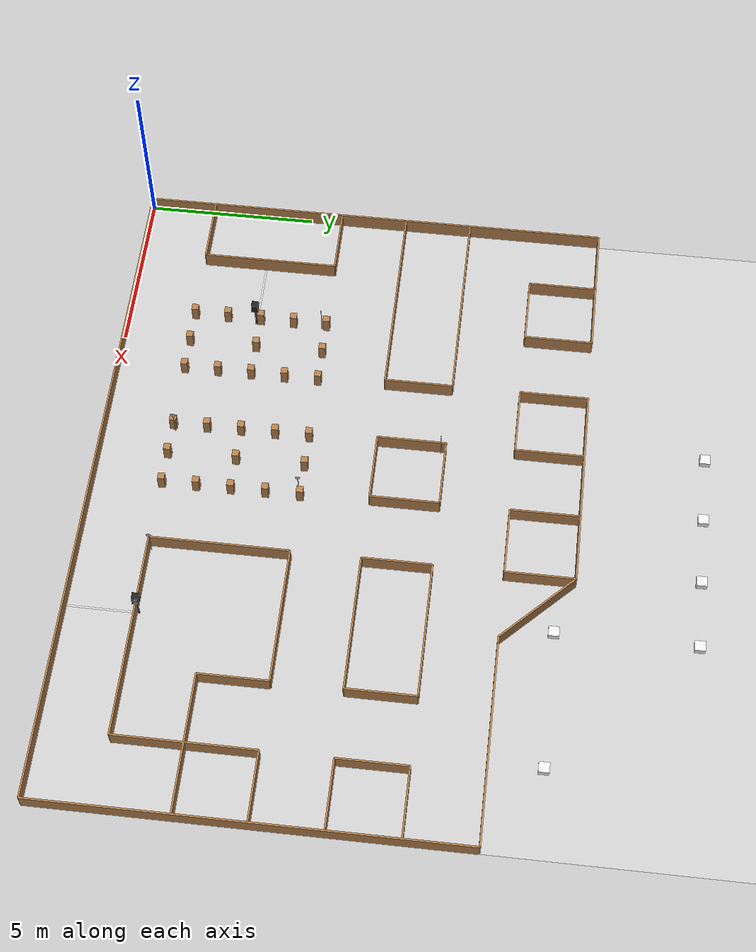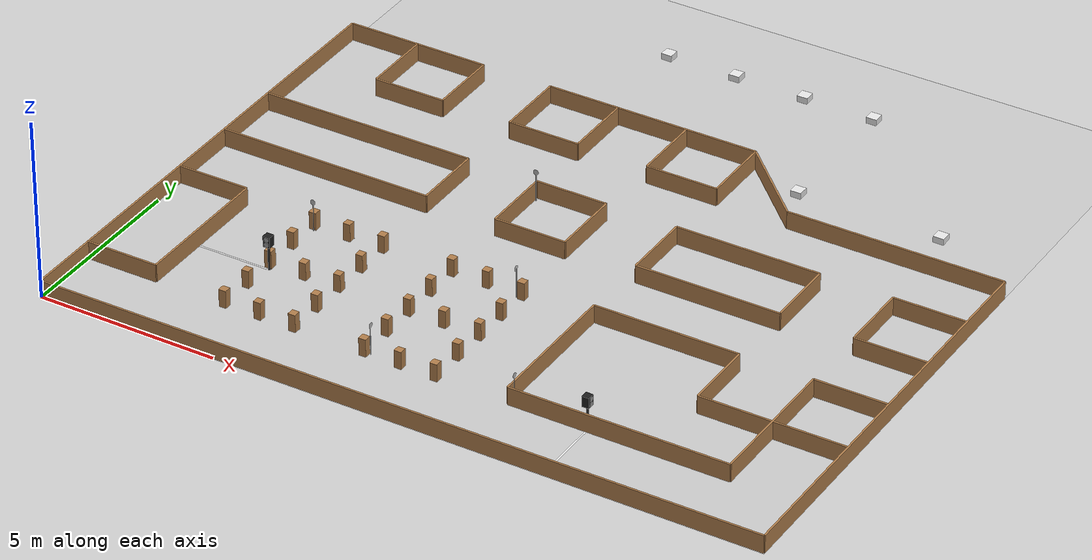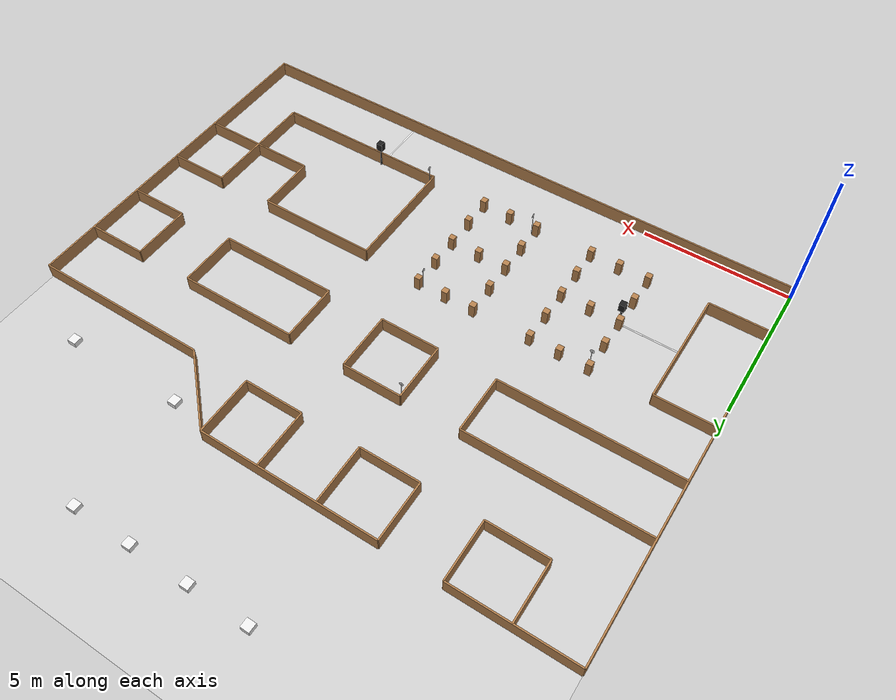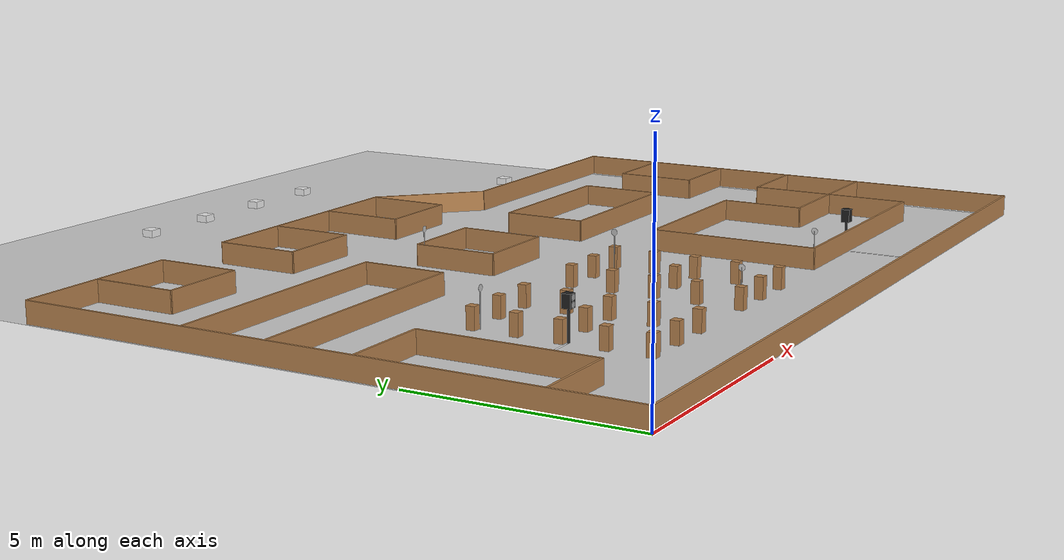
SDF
<sdf version="1.6">
  <world name="default">
    <include><uri>model://cube</uri><name>cube_5</name><pose>13.5 17.5 0 0 0 4.71238898038469</pose></include><include><uri>model://cube</uri><name>cube_4</name><pose>11.5 17.5 0 0 0 4.71238898038469</pose></include><include><uri>model://cube</uri><name>cube_3</name><pose>9.5 17.5 0 0 0 4.71238898038469</pose></include><include><uri>model://cube</uri><name>cube_2</name><pose>7.5 17.5 0 0 0 4.71238898038469</pose></include><include><uri>model://cube</uri><name>cube_1</name><pose>17.5 13.5 0 0 0 4.71238898038469</pose></include><include><uri>model://cube</uri><name>cube_0</name><pose>13.5 13.5 0 0 0 4.71238898038469</pose></include><model name="box_72">
  <pose frame="">10.0 2.0 0.25 0 0 0</pose>
  <link name="link">
    <inertial>
      <mass>1</mass>
      <inertia>
        <ixx>0</ixx>
        <ixy>0</ixy>
        <ixz>0</ixz>
        <iyy>0</iyy>
        <iyz>0</iyz>
        <izz>0</izz>
      </inertia>
    </inertial>
    <collision name="collision">
      <geometry>
        <box>
          <size>0.2 0.2 0.5</size>
        </box>
      </geometry>
      <max_contacts>10</max_contacts>
      <surface>
        <contact>
          <ode/>
        </contact>
        <bounce/>
        <friction>
          <torsional>
            <ode/>
          </torsional>
          <ode/>
        </friction>
      </surface>
    </collision>
    <visual name="visual">
      <geometry>
        <box>
          <size>0.2 0.2 0.5</size>
        </box>
      </geometry>
      <material>
        <script>
          <name>Gazebo/WoodFloor</name>
          <uri>file://media/materials/scripts/gazebo.material</uri>
        </script>
      </material>
    </visual>
    <self_collide>0</self_collide>
    <enable_wind>0</enable_wind>
    <kinematic>0</kinematic>
  </link>
	<static>1</static>
</model><model name="box_71">
  <pose frame="">9.0 2.0 0.25 0 0 0</pose>
  <link name="link">
    <inertial>
      <mass>1</mass>
      <inertia>
        <ixx>0</ixx>
        <ixy>0</ixy>
        <ixz>0</ixz>
        <iyy>0</iyy>
        <iyz>0</iyz>
        <izz>0</izz>
      </inertia>
    </inertial>
    <collision name="collision">
      <geometry>
        <box>
          <size>0.2 0.2 0.5</size>
        </box>
      </geometry>
      <max_contacts>10</max_contacts>
      <surface>
        <contact>
          <ode/>
        </contact>
        <bounce/>
        <friction>
          <torsional>
            <ode/>
          </torsional>
          <ode/>
        </friction>
      </surface>
    </collision>
    <visual name="visual">
      <geometry>
        <box>
          <size>0.2 0.2 0.5</size>
        </box>
      </geometry>
      <material>
        <script>
          <name>Gazebo/WoodFloor</name>
          <uri>file://media/materials/scripts/gazebo.material</uri>
        </script>
      </material>
    </visual>
    <self_collide>0</self_collide>
    <enable_wind>0</enable_wind>
    <kinematic>0</kinematic>
  </link>
	<static>1</static>
</model><model name="box_70">
  <pose frame="">8.0 2.0 0.25 0 0 0</pose>
  <link name="link">
    <inertial>
      <mass>1</mass>
      <inertia>
        <ixx>0</ixx>
        <ixy>0</ixy>
        <ixz>0</ixz>
        <iyy>0</iyy>
        <iyz>0</iyz>
        <izz>0</izz>
      </inertia>
    </inertial>
    <collision name="collision">
      <geometry>
        <box>
          <size>0.2 0.2 0.5</size>
        </box>
      </geometry>
      <max_contacts>10</max_contacts>
      <surface>
        <contact>
          <ode/>
        </contact>
        <bounce/>
        <friction>
          <torsional>
            <ode/>
          </torsional>
          <ode/>
        </friction>
      </surface>
    </collision>
    <visual name="visual">
      <geometry>
        <box>
          <size>0.2 0.2 0.5</size>
        </box>
      </geometry>
      <material>
        <script>
          <name>Gazebo/WoodFloor</name>
          <uri>file://media/materials/scripts/gazebo.material</uri>
        </script>
      </material>
    </visual>
    <self_collide>0</self_collide>
    <enable_wind>0</enable_wind>
    <kinematic>0</kinematic>
  </link>
	<static>1</static>
</model><model name="box_69">
  <pose frame="">10.0 3.0 0.25 0 0 0</pose>
  <link name="link">
    <inertial>
      <mass>1</mass>
      <inertia>
        <ixx>0</ixx>
        <ixy>0</ixy>
        <ixz>0</ixz>
        <iyy>0</iyy>
        <iyz>0</iyz>
        <izz>0</izz>
      </inertia>
    </inertial>
    <collision name="collision">
      <geometry>
        <box>
          <size>0.2 0.2 0.5</size>
        </box>
      </geometry>
      <max_contacts>10</max_contacts>
      <surface>
        <contact>
          <ode/>
        </contact>
        <bounce/>
        <friction>
          <torsional>
            <ode/>
          </torsional>
          <ode/>
        </friction>
      </surface>
    </collision>
    <visual name="visual">
      <geometry>
        <box>
          <size>0.2 0.2 0.5</size>
        </box>
      </geometry>
      <material>
        <script>
          <name>Gazebo/WoodFloor</name>
          <uri>file://media/materials/scripts/gazebo.material</uri>
        </script>
      </material>
    </visual>
    <self_collide>0</self_collide>
    <enable_wind>0</enable_wind>
    <kinematic>0</kinematic>
  </link>
	<static>1</static>
</model><model name="box_68">
  <pose frame="">8.0 3.0 0.25 0 0 0</pose>
  <link name="link">
    <inertial>
      <mass>1</mass>
      <inertia>
        <ixx>0</ixx>
        <ixy>0</ixy>
        <ixz>0</ixz>
        <iyy>0</iyy>
        <iyz>0</iyz>
        <izz>0</izz>
      </inertia>
    </inertial>
    <collision name="collision">
      <geometry>
        <box>
          <size>0.2 0.2 0.5</size>
        </box>
      </geometry>
      <max_contacts>10</max_contacts>
      <surface>
        <contact>
          <ode/>
        </contact>
        <bounce/>
        <friction>
          <torsional>
            <ode/>
          </torsional>
          <ode/>
        </friction>
      </surface>
    </collision>
    <visual name="visual">
      <geometry>
        <box>
          <size>0.2 0.2 0.5</size>
        </box>
      </geometry>
      <material>
        <script>
          <name>Gazebo/WoodFloor</name>
          <uri>file://media/materials/scripts/gazebo.material</uri>
        </script>
      </material>
    </visual>
    <self_collide>0</self_collide>
    <enable_wind>0</enable_wind>
    <kinematic>0</kinematic>
  </link>
	<static>1</static>
</model><model name="box_67">
  <pose frame="">10.0 4.0 0.25 0 0 0</pose>
  <link name="link">
    <inertial>
      <mass>1</mass>
      <inertia>
        <ixx>0</ixx>
        <ixy>0</ixy>
        <ixz>0</ixz>
        <iyy>0</iyy>
        <iyz>0</iyz>
        <izz>0</izz>
      </inertia>
    </inertial>
    <collision name="collision">
      <geometry>
        <box>
          <size>0.2 0.2 0.5</size>
        </box>
      </geometry>
      <max_contacts>10</max_contacts>
      <surface>
        <contact>
          <ode/>
        </contact>
        <bounce/>
        <friction>
          <torsional>
            <ode/>
          </torsional>
          <ode/>
        </friction>
      </surface>
    </collision>
    <visual name="visual">
      <geometry>
        <box>
          <size>0.2 0.2 0.5</size>
        </box>
      </geometry>
      <material>
        <script>
          <name>Gazebo/WoodFloor</name>
          <uri>file://media/materials/scripts/gazebo.material</uri>
        </script>
      </material>
    </visual>
    <self_collide>0</self_collide>
    <enable_wind>0</enable_wind>
    <kinematic>0</kinematic>
  </link>
	<static>1</static>
</model><model name="box_66">
  <pose frame="">9.0 4.0 0.25 0 0 0</pose>
  <link name="link">
    <inertial>
      <mass>1</mass>
      <inertia>
        <ixx>0</ixx>
        <ixy>0</ixy>
        <ixz>0</ixz>
        <iyy>0</iyy>
        <iyz>0</iyz>
        <izz>0</izz>
      </inertia>
    </inertial>
    <collision name="collision">
      <geometry>
        <box>
          <size>0.2 0.2 0.5</size>
        </box>
      </geometry>
      <max_contacts>10</max_contacts>
      <surface>
        <contact>
          <ode/>
        </contact>
        <bounce/>
        <friction>
          <torsional>
            <ode/>
          </torsional>
          <ode/>
        </friction>
      </surface>
    </collision>
    <visual name="visual">
      <geometry>
        <box>
          <size>0.2 0.2 0.5</size>
        </box>
      </geometry>
      <material>
        <script>
          <name>Gazebo/WoodFloor</name>
          <uri>file://media/materials/scripts/gazebo.material</uri>
        </script>
      </material>
    </visual>
    <self_collide>0</self_collide>
    <enable_wind>0</enable_wind>
    <kinematic>0</kinematic>
  </link>
	<static>1</static>
</model><model name="box_65">
  <pose frame="">8.0 4.0 0.25 0 0 0</pose>
  <link name="link">
    <inertial>
      <mass>1</mass>
      <inertia>
        <ixx>0</ixx>
        <ixy>0</ixy>
        <ixz>0</ixz>
        <iyy>0</iyy>
        <iyz>0</iyz>
        <izz>0</izz>
      </inertia>
    </inertial>
    <collision name="collision">
      <geometry>
        <box>
          <size>0.2 0.2 0.5</size>
        </box>
      </geometry>
      <max_contacts>10</max_contacts>
      <surface>
        <contact>
          <ode/>
        </contact>
        <bounce/>
        <friction>
          <torsional>
            <ode/>
          </torsional>
          <ode/>
        </friction>
      </surface>
    </collision>
    <visual name="visual">
      <geometry>
        <box>
          <size>0.2 0.2 0.5</size>
        </box>
      </geometry>
      <material>
        <script>
          <name>Gazebo/WoodFloor</name>
          <uri>file://media/materials/scripts/gazebo.material</uri>
        </script>
      </material>
    </visual>
    <self_collide>0</self_collide>
    <enable_wind>0</enable_wind>
    <kinematic>0</kinematic>
  </link>
	<static>1</static>
</model><model name="box_64">
  <pose frame="">10.0 4.0 0.25 0 0 0</pose>
  <link name="link">
    <inertial>
      <mass>1</mass>
      <inertia>
        <ixx>0</ixx>
        <ixy>0</ixy>
        <ixz>0</ixz>
        <iyy>0</iyy>
        <iyz>0</iyz>
        <izz>0</izz>
      </inertia>
    </inertial>
    <collision name="collision">
      <geometry>
        <box>
          <size>0.2 0.2 0.5</size>
        </box>
      </geometry>
      <max_contacts>10</max_contacts>
      <surface>
        <contact>
          <ode/>
        </contact>
        <bounce/>
        <friction>
          <torsional>
            <ode/>
          </torsional>
          <ode/>
        </friction>
      </surface>
    </collision>
    <visual name="visual">
      <geometry>
        <box>
          <size>0.2 0.2 0.5</size>
        </box>
      </geometry>
      <material>
        <script>
          <name>Gazebo/WoodFloor</name>
          <uri>file://media/materials/scripts/gazebo.material</uri>
        </script>
      </material>
    </visual>
    <self_collide>0</self_collide>
    <enable_wind>0</enable_wind>
    <kinematic>0</kinematic>
  </link>
	<static>1</static>
</model><model name="box_63">
  <pose frame="">9.0 4.0 0.25 0 0 0</pose>
  <link name="link">
    <inertial>
      <mass>1</mass>
      <inertia>
        <ixx>0</ixx>
        <ixy>0</ixy>
        <ixz>0</ixz>
        <iyy>0</iyy>
        <iyz>0</iyz>
        <izz>0</izz>
      </inertia>
    </inertial>
    <collision name="collision">
      <geometry>
        <box>
          <size>0.2 0.2 0.5</size>
        </box>
      </geometry>
      <max_contacts>10</max_contacts>
      <surface>
        <contact>
          <ode/>
        </contact>
        <bounce/>
        <friction>
          <torsional>
            <ode/>
          </torsional>
          <ode/>
        </friction>
      </surface>
    </collision>
    <visual name="visual">
      <geometry>
        <box>
          <size>0.2 0.2 0.5</size>
        </box>
      </geometry>
      <material>
        <script>
          <name>Gazebo/WoodFloor</name>
          <uri>file://media/materials/scripts/gazebo.material</uri>
        </script>
      </material>
    </visual>
    <self_collide>0</self_collide>
    <enable_wind>0</enable_wind>
    <kinematic>0</kinematic>
  </link>
	<static>1</static>
</model><model name="box_62">
  <pose frame="">8.0 4.0 0.25 0 0 0</pose>
  <link name="link">
    <inertial>
      <mass>1</mass>
      <inertia>
        <ixx>0</ixx>
        <ixy>0</ixy>
        <ixz>0</ixz>
        <iyy>0</iyy>
        <iyz>0</iyz>
        <izz>0</izz>
      </inertia>
    </inertial>
    <collision name="collision">
      <geometry>
        <box>
          <size>0.2 0.2 0.5</size>
        </box>
      </geometry>
      <max_contacts>10</max_contacts>
      <surface>
        <contact>
          <ode/>
        </contact>
        <bounce/>
        <friction>
          <torsional>
            <ode/>
          </torsional>
          <ode/>
        </friction>
      </surface>
    </collision>
    <visual name="visual">
      <geometry>
        <box>
          <size>0.2 0.2 0.5</size>
        </box>
      </geometry>
      <material>
        <script>
          <name>Gazebo/WoodFloor</name>
          <uri>file://media/materials/scripts/gazebo.material</uri>
        </script>
      </material>
    </visual>
    <self_collide>0</self_collide>
    <enable_wind>0</enable_wind>
    <kinematic>0</kinematic>
  </link>
	<static>1</static>
</model><model name="box_61">
  <pose frame="">10.0 5.0 0.25 0 0 0</pose>
  <link name="link">
    <inertial>
      <mass>1</mass>
      <inertia>
        <ixx>0</ixx>
        <ixy>0</ixy>
        <ixz>0</ixz>
        <iyy>0</iyy>
        <iyz>0</iyz>
        <izz>0</izz>
      </inertia>
    </inertial>
    <collision name="collision">
      <geometry>
        <box>
          <size>0.2 0.2 0.5</size>
        </box>
      </geometry>
      <max_contacts>10</max_contacts>
      <surface>
        <contact>
          <ode/>
        </contact>
        <bounce/>
        <friction>
          <torsional>
            <ode/>
          </torsional>
          <ode/>
        </friction>
      </surface>
    </collision>
    <visual name="visual">
      <geometry>
        <box>
          <size>0.2 0.2 0.5</size>
        </box>
      </geometry>
      <material>
        <script>
          <name>Gazebo/WoodFloor</name>
          <uri>file://media/materials/scripts/gazebo.material</uri>
        </script>
      </material>
    </visual>
    <self_collide>0</self_collide>
    <enable_wind>0</enable_wind>
    <kinematic>0</kinematic>
  </link>
	<static>1</static>
</model><model name="box_60">
  <pose frame="">8.0 5.0 0.25 0 0 0</pose>
  <link name="link">
    <inertial>
      <mass>1</mass>
      <inertia>
        <ixx>0</ixx>
        <ixy>0</ixy>
        <ixz>0</ixz>
        <iyy>0</iyy>
        <iyz>0</iyz>
        <izz>0</izz>
      </inertia>
    </inertial>
    <collision name="collision">
      <geometry>
        <box>
          <size>0.2 0.2 0.5</size>
        </box>
      </geometry>
      <max_contacts>10</max_contacts>
      <surface>
        <contact>
          <ode/>
        </contact>
        <bounce/>
        <friction>
          <torsional>
            <ode/>
          </torsional>
          <ode/>
        </friction>
      </surface>
    </collision>
    <visual name="visual">
      <geometry>
        <box>
          <size>0.2 0.2 0.5</size>
        </box>
      </geometry>
      <material>
        <script>
          <name>Gazebo/WoodFloor</name>
          <uri>file://media/materials/scripts/gazebo.material</uri>
        </script>
      </material>
    </visual>
    <self_collide>0</self_collide>
    <enable_wind>0</enable_wind>
    <kinematic>0</kinematic>
  </link>
	<static>1</static>
</model><model name="box_59">
  <pose frame="">10.0 6.0 0.25 0 0 0</pose>
  <link name="link">
    <inertial>
      <mass>1</mass>
      <inertia>
        <ixx>0</ixx>
        <ixy>0</ixy>
        <ixz>0</ixz>
        <iyy>0</iyy>
        <iyz>0</iyz>
        <izz>0</izz>
      </inertia>
    </inertial>
    <collision name="collision">
      <geometry>
        <box>
          <size>0.2 0.2 0.5</size>
        </box>
      </geometry>
      <max_contacts>10</max_contacts>
      <surface>
        <contact>
          <ode/>
        </contact>
        <bounce/>
        <friction>
          <torsional>
            <ode/>
          </torsional>
          <ode/>
        </friction>
      </surface>
    </collision>
    <visual name="visual">
      <geometry>
        <box>
          <size>0.2 0.2 0.5</size>
        </box>
      </geometry>
      <material>
        <script>
          <name>Gazebo/WoodFloor</name>
          <uri>file://media/materials/scripts/gazebo.material</uri>
        </script>
      </material>
    </visual>
    <self_collide>0</self_collide>
    <enable_wind>0</enable_wind>
    <kinematic>0</kinematic>
  </link>
	<static>1</static>
</model><model name="box_58">
  <pose frame="">9.0 6.0 0.25 0 0 0</pose>
  <link name="link">
    <inertial>
      <mass>1</mass>
      <inertia>
        <ixx>0</ixx>
        <ixy>0</ixy>
        <ixz>0</ixz>
        <iyy>0</iyy>
        <iyz>0</iyz>
        <izz>0</izz>
      </inertia>
    </inertial>
    <collision name="collision">
      <geometry>
        <box>
          <size>0.2 0.2 0.5</size>
        </box>
      </geometry>
      <max_contacts>10</max_contacts>
      <surface>
        <contact>
          <ode/>
        </contact>
        <bounce/>
        <friction>
          <torsional>
            <ode/>
          </torsional>
          <ode/>
        </friction>
      </surface>
    </collision>
    <visual name="visual">
      <geometry>
        <box>
          <size>0.2 0.2 0.5</size>
        </box>
      </geometry>
      <material>
        <script>
          <name>Gazebo/WoodFloor</name>
          <uri>file://media/materials/scripts/gazebo.material</uri>
        </script>
      </material>
    </visual>
    <self_collide>0</self_collide>
    <enable_wind>0</enable_wind>
    <kinematic>0</kinematic>
  </link>
	<static>1</static>
</model><model name="box_57">
  <pose frame="">8.0 6.0 0.25 0 0 0</pose>
  <link name="link">
    <inertial>
      <mass>1</mass>
      <inertia>
        <ixx>0</ixx>
        <ixy>0</ixy>
        <ixz>0</ixz>
        <iyy>0</iyy>
        <iyz>0</iyz>
        <izz>0</izz>
      </inertia>
    </inertial>
    <collision name="collision">
      <geometry>
        <box>
          <size>0.2 0.2 0.5</size>
        </box>
      </geometry>
      <max_contacts>10</max_contacts>
      <surface>
        <contact>
          <ode/>
        </contact>
        <bounce/>
        <friction>
          <torsional>
            <ode/>
          </torsional>
          <ode/>
        </friction>
      </surface>
    </collision>
    <visual name="visual">
      <geometry>
        <box>
          <size>0.2 0.2 0.5</size>
        </box>
      </geometry>
      <material>
        <script>
          <name>Gazebo/WoodFloor</name>
          <uri>file://media/materials/scripts/gazebo.material</uri>
        </script>
      </material>
    </visual>
    <self_collide>0</self_collide>
    <enable_wind>0</enable_wind>
    <kinematic>0</kinematic>
  </link>
	<static>1</static>
</model><model name="box_56">
  <pose frame="">6.0 2.0 0.25 0 0 0</pose>
  <link name="link">
    <inertial>
      <mass>1</mass>
      <inertia>
        <ixx>0</ixx>
        <ixy>0</ixy>
        <ixz>0</ixz>
        <iyy>0</iyy>
        <iyz>0</iyz>
        <izz>0</izz>
      </inertia>
    </inertial>
    <collision name="collision">
      <geometry>
        <box>
          <size>0.2 0.2 0.5</size>
        </box>
      </geometry>
      <max_contacts>10</max_contacts>
      <surface>
        <contact>
          <ode/>
        </contact>
        <bounce/>
        <friction>
          <torsional>
            <ode/>
          </torsional>
          <ode/>
        </friction>
      </surface>
    </collision>
    <visual name="visual">
      <geometry>
        <box>
          <size>0.2 0.2 0.5</size>
        </box>
      </geometry>
      <material>
        <script>
          <name>Gazebo/WoodFloor</name>
          <uri>file://media/materials/scripts/gazebo.material</uri>
        </script>
      </material>
    </visual>
    <self_collide>0</self_collide>
    <enable_wind>0</enable_wind>
    <kinematic>0</kinematic>
  </link>
	<static>1</static>
</model><model name="box_55">
  <pose frame="">5.0 2.0 0.25 0 0 0</pose>
  <link name="link">
    <inertial>
      <mass>1</mass>
      <inertia>
        <ixx>0</ixx>
        <ixy>0</ixy>
        <ixz>0</ixz>
        <iyy>0</iyy>
        <iyz>0</iyz>
        <izz>0</izz>
      </inertia>
    </inertial>
    <collision name="collision">
      <geometry>
        <box>
          <size>0.2 0.2 0.5</size>
        </box>
      </geometry>
      <max_contacts>10</max_contacts>
      <surface>
        <contact>
          <ode/>
        </contact>
        <bounce/>
        <friction>
          <torsional>
            <ode/>
          </torsional>
          <ode/>
        </friction>
      </surface>
    </collision>
    <visual name="visual">
      <geometry>
        <box>
          <size>0.2 0.2 0.5</size>
        </box>
      </geometry>
      <material>
        <script>
          <name>Gazebo/WoodFloor</name>
          <uri>file://media/materials/scripts/gazebo.material</uri>
        </script>
      </material>
    </visual>
    <self_collide>0</self_collide>
    <enable_wind>0</enable_wind>
    <kinematic>0</kinematic>
  </link>
	<static>1</static>
</model><model name="box_54">
  <pose frame="">4.0 2.0 0.25 0 0 0</pose>
  <link name="link">
    <inertial>
      <mass>1</mass>
      <inertia>
        <ixx>0</ixx>
        <ixy>0</ixy>
        <ixz>0</ixz>
        <iyy>0</iyy>
        <iyz>0</iyz>
        <izz>0</izz>
      </inertia>
    </inertial>
    <collision name="collision">
      <geometry>
        <box>
          <size>0.2 0.2 0.5</size>
        </box>
      </geometry>
      <max_contacts>10</max_contacts>
      <surface>
        <contact>
          <ode/>
        </contact>
        <bounce/>
        <friction>
          <torsional>
            <ode/>
          </torsional>
          <ode/>
        </friction>
      </surface>
    </collision>
    <visual name="visual">
      <geometry>
        <box>
          <size>0.2 0.2 0.5</size>
        </box>
      </geometry>
      <material>
        <script>
          <name>Gazebo/WoodFloor</name>
          <uri>file://media/materials/scripts/gazebo.material</uri>
        </script>
      </material>
    </visual>
    <self_collide>0</self_collide>
    <enable_wind>0</enable_wind>
    <kinematic>0</kinematic>
  </link>
	<static>1</static>
</model><model name="box_53">
  <pose frame="">6.0 3.0 0.25 0 0 0</pose>
  <link name="link">
    <inertial>
      <mass>1</mass>
      <inertia>
        <ixx>0</ixx>
        <ixy>0</ixy>
        <ixz>0</ixz>
        <iyy>0</iyy>
        <iyz>0</iyz>
        <izz>0</izz>
      </inertia>
    </inertial>
    <collision name="collision">
      <geometry>
        <box>
          <size>0.2 0.2 0.5</size>
        </box>
      </geometry>
      <max_contacts>10</max_contacts>
      <surface>
        <contact>
          <ode/>
        </contact>
        <bounce/>
        <friction>
          <torsional>
            <ode/>
          </torsional>
          <ode/>
        </friction>
      </surface>
    </collision>
    <visual name="visual">
      <geometry>
        <box>
          <size>0.2 0.2 0.5</size>
        </box>
      </geometry>
      <material>
        <script>
          <name>Gazebo/WoodFloor</name>
          <uri>file://media/materials/scripts/gazebo.material</uri>
        </script>
      </material>
    </visual>
    <self_collide>0</self_collide>
    <enable_wind>0</enable_wind>
    <kinematic>0</kinematic>
  </link>
	<static>1</static>
</model><model name="box_52">
  <pose frame="">4.0 3.0 0.25 0 0 0</pose>
  <link name="link">
    <inertial>
      <mass>1</mass>
      <inertia>
        <ixx>0</ixx>
        <ixy>0</ixy>
        <ixz>0</ixz>
        <iyy>0</iyy>
        <iyz>0</iyz>
        <izz>0</izz>
      </inertia>
    </inertial>
    <collision name="collision">
      <geometry>
        <box>
          <size>0.2 0.2 0.5</size>
        </box>
      </geometry>
      <max_contacts>10</max_contacts>
      <surface>
        <contact>
          <ode/>
        </contact>
        <bounce/>
        <friction>
          <torsional>
            <ode/>
          </torsional>
          <ode/>
        </friction>
      </surface>
    </collision>
    <visual name="visual">
      <geometry>
        <box>
          <size>0.2 0.2 0.5</size>
        </box>
      </geometry>
      <material>
        <script>
          <name>Gazebo/WoodFloor</name>
          <uri>file://media/materials/scripts/gazebo.material</uri>
        </script>
      </material>
    </visual>
    <self_collide>0</self_collide>
    <enable_wind>0</enable_wind>
    <kinematic>0</kinematic>
  </link>
	<static>1</static>
</model><model name="box_51">
  <pose frame="">6.0 4.0 0.25 0 0 0</pose>
  <link name="link">
    <inertial>
      <mass>1</mass>
      <inertia>
        <ixx>0</ixx>
        <ixy>0</ixy>
        <ixz>0</ixz>
        <iyy>0</iyy>
        <iyz>0</iyz>
        <izz>0</izz>
      </inertia>
    </inertial>
    <collision name="collision">
      <geometry>
        <box>
          <size>0.2 0.2 0.5</size>
        </box>
      </geometry>
      <max_contacts>10</max_contacts>
      <surface>
        <contact>
          <ode/>
        </contact>
        <bounce/>
        <friction>
          <torsional>
            <ode/>
          </torsional>
          <ode/>
        </friction>
      </surface>
    </collision>
    <visual name="visual">
      <geometry>
        <box>
          <size>0.2 0.2 0.5</size>
        </box>
      </geometry>
      <material>
        <script>
          <name>Gazebo/WoodFloor</name>
          <uri>file://media/materials/scripts/gazebo.material</uri>
        </script>
      </material>
    </visual>
    <self_collide>0</self_collide>
    <enable_wind>0</enable_wind>
    <kinematic>0</kinematic>
  </link>
	<static>1</static>
</model><model name="box_50">
  <pose frame="">5.0 4.0 0.25 0 0 0</pose>
  <link name="link">
    <inertial>
      <mass>1</mass>
      <inertia>
        <ixx>0</ixx>
        <ixy>0</ixy>
        <ixz>0</ixz>
        <iyy>0</iyy>
        <iyz>0</iyz>
        <izz>0</izz>
      </inertia>
    </inertial>
    <collision name="collision">
      <geometry>
        <box>
          <size>0.2 0.2 0.5</size>
        </box>
      </geometry>
      <max_contacts>10</max_contacts>
      <surface>
        <contact>
          <ode/>
        </contact>
        <bounce/>
        <friction>
          <torsional>
            <ode/>
          </torsional>
          <ode/>
        </friction>
      </surface>
    </collision>
    <visual name="visual">
      <geometry>
        <box>
          <size>0.2 0.2 0.5</size>
        </box>
      </geometry>
      <material>
        <script>
          <name>Gazebo/WoodFloor</name>
          <uri>file://media/materials/scripts/gazebo.material</uri>
        </script>
      </material>
    </visual>
    <self_collide>0</self_collide>
    <enable_wind>0</enable_wind>
    <kinematic>0</kinematic>
  </link>
	<static>1</static>
</model><model name="box_49">
  <pose frame="">4.0 4.0 0.25 0 0 0</pose>
  <link name="link">
    <inertial>
      <mass>1</mass>
      <inertia>
        <ixx>0</ixx>
        <ixy>0</ixy>
        <ixz>0</ixz>
        <iyy>0</iyy>
        <iyz>0</iyz>
        <izz>0</izz>
      </inertia>
    </inertial>
    <collision name="collision">
      <geometry>
        <box>
          <size>0.2 0.2 0.5</size>
        </box>
      </geometry>
      <max_contacts>10</max_contacts>
      <surface>
        <contact>
          <ode/>
        </contact>
        <bounce/>
        <friction>
          <torsional>
            <ode/>
          </torsional>
          <ode/>
        </friction>
      </surface>
    </collision>
    <visual name="visual">
      <geometry>
        <box>
          <size>0.2 0.2 0.5</size>
        </box>
      </geometry>
      <material>
        <script>
          <name>Gazebo/WoodFloor</name>
          <uri>file://media/materials/scripts/gazebo.material</uri>
        </script>
      </material>
    </visual>
    <self_collide>0</self_collide>
    <enable_wind>0</enable_wind>
    <kinematic>0</kinematic>
  </link>
	<static>1</static>
</model><model name="box_48">
  <pose frame="">6.0 4.0 0.25 0 0 0</pose>
  <link name="link">
    <inertial>
      <mass>1</mass>
      <inertia>
        <ixx>0</ixx>
        <ixy>0</ixy>
        <ixz>0</ixz>
        <iyy>0</iyy>
        <iyz>0</iyz>
        <izz>0</izz>
      </inertia>
    </inertial>
    <collision name="collision">
      <geometry>
        <box>
          <size>0.2 0.2 0.5</size>
        </box>
      </geometry>
      <max_contacts>10</max_contacts>
      <surface>
        <contact>
          <ode/>
        </contact>
        <bounce/>
        <friction>
          <torsional>
            <ode/>
          </torsional>
          <ode/>
        </friction>
      </surface>
    </collision>
    <visual name="visual">
      <geometry>
        <box>
          <size>0.2 0.2 0.5</size>
        </box>
      </geometry>
      <material>
        <script>
          <name>Gazebo/WoodFloor</name>
          <uri>file://media/materials/scripts/gazebo.material</uri>
        </script>
      </material>
    </visual>
    <self_collide>0</self_collide>
    <enable_wind>0</enable_wind>
    <kinematic>0</kinematic>
  </link>
	<static>1</static>
</model><model name="box_47">
  <pose frame="">5.0 4.0 0.25 0 0 0</pose>
  <link name="link">
    <inertial>
      <mass>1</mass>
      <inertia>
        <ixx>0</ixx>
        <ixy>0</ixy>
        <ixz>0</ixz>
        <iyy>0</iyy>
        <iyz>0</iyz>
        <izz>0</izz>
      </inertia>
    </inertial>
    <collision name="collision">
      <geometry>
        <box>
          <size>0.2 0.2 0.5</size>
        </box>
      </geometry>
      <max_contacts>10</max_contacts>
      <surface>
        <contact>
          <ode/>
        </contact>
        <bounce/>
        <friction>
          <torsional>
            <ode/>
          </torsional>
          <ode/>
        </friction>
      </surface>
    </collision>
    <visual name="visual">
      <geometry>
        <box>
          <size>0.2 0.2 0.5</size>
        </box>
      </geometry>
      <material>
        <script>
          <name>Gazebo/WoodFloor</name>
          <uri>file://media/materials/scripts/gazebo.material</uri>
        </script>
      </material>
    </visual>
    <self_collide>0</self_collide>
    <enable_wind>0</enable_wind>
    <kinematic>0</kinematic>
  </link>
	<static>1</static>
</model><model name="box_46">
  <pose frame="">4.0 4.0 0.25 0 0 0</pose>
  <link name="link">
    <inertial>
      <mass>1</mass>
      <inertia>
        <ixx>0</ixx>
        <ixy>0</ixy>
        <ixz>0</ixz>
        <iyy>0</iyy>
        <iyz>0</iyz>
        <izz>0</izz>
      </inertia>
    </inertial>
    <collision name="collision">
      <geometry>
        <box>
          <size>0.2 0.2 0.5</size>
        </box>
      </geometry>
      <max_contacts>10</max_contacts>
      <surface>
        <contact>
          <ode/>
        </contact>
        <bounce/>
        <friction>
          <torsional>
            <ode/>
          </torsional>
          <ode/>
        </friction>
      </surface>
    </collision>
    <visual name="visual">
      <geometry>
        <box>
          <size>0.2 0.2 0.5</size>
        </box>
      </geometry>
      <material>
        <script>
          <name>Gazebo/WoodFloor</name>
          <uri>file://media/materials/scripts/gazebo.material</uri>
        </script>
      </material>
    </visual>
    <self_collide>0</self_collide>
    <enable_wind>0</enable_wind>
    <kinematic>0</kinematic>
  </link>
	<static>1</static>
</model><model name="box_45">
  <pose frame="">6.0 5.0 0.25 0 0 0</pose>
  <link name="link">
    <inertial>
      <mass>1</mass>
      <inertia>
        <ixx>0</ixx>
        <ixy>0</ixy>
        <ixz>0</ixz>
        <iyy>0</iyy>
        <iyz>0</iyz>
        <izz>0</izz>
      </inertia>
    </inertial>
    <collision name="collision">
      <geometry>
        <box>
          <size>0.2 0.2 0.5</size>
        </box>
      </geometry>
      <max_contacts>10</max_contacts>
      <surface>
        <contact>
          <ode/>
        </contact>
        <bounce/>
        <friction>
          <torsional>
            <ode/>
          </torsional>
          <ode/>
        </friction>
      </surface>
    </collision>
    <visual name="visual">
      <geometry>
        <box>
          <size>0.2 0.2 0.5</size>
        </box>
      </geometry>
      <material>
        <script>
          <name>Gazebo/WoodFloor</name>
          <uri>file://media/materials/scripts/gazebo.material</uri>
        </script>
      </material>
    </visual>
    <self_collide>0</self_collide>
    <enable_wind>0</enable_wind>
    <kinematic>0</kinematic>
  </link>
	<static>1</static>
</model><model name="box_44">
  <pose frame="">4.0 5.0 0.25 0 0 0</pose>
  <link name="link">
    <inertial>
      <mass>1</mass>
      <inertia>
        <ixx>0</ixx>
        <ixy>0</ixy>
        <ixz>0</ixz>
        <iyy>0</iyy>
        <iyz>0</iyz>
        <izz>0</izz>
      </inertia>
    </inertial>
    <collision name="collision">
      <geometry>
        <box>
          <size>0.2 0.2 0.5</size>
        </box>
      </geometry>
      <max_contacts>10</max_contacts>
      <surface>
        <contact>
          <ode/>
        </contact>
        <bounce/>
        <friction>
          <torsional>
            <ode/>
          </torsional>
          <ode/>
        </friction>
      </surface>
    </collision>
    <visual name="visual">
      <geometry>
        <box>
          <size>0.2 0.2 0.5</size>
        </box>
      </geometry>
      <material>
        <script>
          <name>Gazebo/WoodFloor</name>
          <uri>file://media/materials/scripts/gazebo.material</uri>
        </script>
      </material>
    </visual>
    <self_collide>0</self_collide>
    <enable_wind>0</enable_wind>
    <kinematic>0</kinematic>
  </link>
	<static>1</static>
</model><model name="box_43">
  <pose frame="">6.0 6.0 0.25 0 0 0</pose>
  <link name="link">
    <inertial>
      <mass>1</mass>
      <inertia>
        <ixx>0</ixx>
        <ixy>0</ixy>
        <ixz>0</ixz>
        <iyy>0</iyy>
        <iyz>0</iyz>
        <izz>0</izz>
      </inertia>
    </inertial>
    <collision name="collision">
      <geometry>
        <box>
          <size>0.2 0.2 0.5</size>
        </box>
      </geometry>
      <max_contacts>10</max_contacts>
      <surface>
        <contact>
          <ode/>
        </contact>
        <bounce/>
        <friction>
          <torsional>
            <ode/>
          </torsional>
          <ode/>
        </friction>
      </surface>
    </collision>
    <visual name="visual">
      <geometry>
        <box>
          <size>0.2 0.2 0.5</size>
        </box>
      </geometry>
      <material>
        <script>
          <name>Gazebo/WoodFloor</name>
          <uri>file://media/materials/scripts/gazebo.material</uri>
        </script>
      </material>
    </visual>
    <self_collide>0</self_collide>
    <enable_wind>0</enable_wind>
    <kinematic>0</kinematic>
  </link>
	<static>1</static>
</model><model name="box_42">
  <pose frame="">5.0 6.0 0.25 0 0 0</pose>
  <link name="link">
    <inertial>
      <mass>1</mass>
      <inertia>
        <ixx>0</ixx>
        <ixy>0</ixy>
        <ixz>0</ixz>
        <iyy>0</iyy>
        <iyz>0</iyz>
        <izz>0</izz>
      </inertia>
    </inertial>
    <collision name="collision">
      <geometry>
        <box>
          <size>0.2 0.2 0.5</size>
        </box>
      </geometry>
      <max_contacts>10</max_contacts>
      <surface>
        <contact>
          <ode/>
        </contact>
        <bounce/>
        <friction>
          <torsional>
            <ode/>
          </torsional>
          <ode/>
        </friction>
      </surface>
    </collision>
    <visual name="visual">
      <geometry>
        <box>
          <size>0.2 0.2 0.5</size>
        </box>
      </geometry>
      <material>
        <script>
          <name>Gazebo/WoodFloor</name>
          <uri>file://media/materials/scripts/gazebo.material</uri>
        </script>
      </material>
    </visual>
    <self_collide>0</self_collide>
    <enable_wind>0</enable_wind>
    <kinematic>0</kinematic>
  </link>
	<static>1</static>
</model><model name="box_41">
  <pose frame="">4.0 6.0 0.25 0 0 0</pose>
  <link name="link">
    <inertial>
      <mass>1</mass>
      <inertia>
        <ixx>0</ixx>
        <ixy>0</ixy>
        <ixz>0</ixz>
        <iyy>0</iyy>
        <iyz>0</iyz>
        <izz>0</izz>
      </inertia>
    </inertial>
    <collision name="collision">
      <geometry>
        <box>
          <size>0.2 0.2 0.5</size>
        </box>
      </geometry>
      <max_contacts>10</max_contacts>
      <surface>
        <contact>
          <ode/>
        </contact>
        <bounce/>
        <friction>
          <torsional>
            <ode/>
          </torsional>
          <ode/>
        </friction>
      </surface>
    </collision>
    <visual name="visual">
      <geometry>
        <box>
          <size>0.2 0.2 0.5</size>
        </box>
      </geometry>
      <material>
        <script>
          <name>Gazebo/WoodFloor</name>
          <uri>file://media/materials/scripts/gazebo.material</uri>
        </script>
      </material>
    </visual>
    <self_collide>0</self_collide>
    <enable_wind>0</enable_wind>
    <kinematic>0</kinematic>
  </link>
	<static>1</static>
</model><include><uri>model://left-sign</uri><name>sign_4</name><pose>8.06 9.86 0 0 0 6.283185307179586</pose></include><include><uri>model://brick-sign</uri><name>sign_3</name><pose>9.86 5.9399999999999995 0 0 0 4.71238898038469</pose></include><include><uri>model://right-sign</uri><name>sign_2</name><pose>4.06 5.859999999999999 0 0 0 6.283185307179586</pose></include><include><uri>model://forward-sign</uri><name>sign_1</name><pose>12.14 2.0600000000000005 0 0 0 1.5707963267948966</pose></include><include><uri>model://forward-sign</uri><name>sign_0</name><pose>8.14 2.0600000000000005 0 0 0 1.5707963267948966</pose></include><model name="box_40">
  <pose frame="">12.0 13.0 0.25 0 0 -1.5707963267948966</pose>
  <link name="link">
    <inertial>
      <mass>1</mass>
      <inertia>
        <ixx>0</ixx>
        <ixy>0</ixy>
        <ixz>0</ixz>
        <iyy>0</iyy>
        <iyz>0</iyz>
        <izz>0</izz>
      </inertia>
    </inertial>
    <collision name="collision">
      <geometry>
        <box>
          <size>2.0 0.05 0.5</size>
        </box>
      </geometry>
      <max_contacts>10</max_contacts>
      <surface>
        <contact>
          <ode/>
        </contact>
        <bounce/>
        <friction>
          <torsional>
            <ode/>
          </torsional>
          <ode/>
        </friction>
      </surface>
    </collision>
    <visual name="visual">
      <geometry>
        <box>
          <size>2.0 0.05 0.5</size>
        </box>
      </geometry>
      <material>
        <script>
          <name>Gazebo/WoodFloor</name>
          <uri>file://media/materials/scripts/gazebo.material</uri>
        </script>
      </material>
    </visual>
    <self_collide>0</self_collide>
    <enable_wind>0</enable_wind>
    <kinematic>0</kinematic>
  </link>
	<static>1</static>
</model><model name="box_39">
  <pose frame="">11.0 12.0 0.25 0 0 -3.141592653589793</pose>
  <link name="link">
    <inertial>
      <mass>1</mass>
      <inertia>
        <ixx>0</ixx>
        <ixy>0</ixy>
        <ixz>0</ixz>
        <iyy>0</iyy>
        <iyz>0</iyz>
        <izz>0</izz>
      </inertia>
    </inertial>
    <collision name="collision">
      <geometry>
        <box>
          <size>2.0 0.05 0.5</size>
        </box>
      </geometry>
      <max_contacts>10</max_contacts>
      <surface>
        <contact>
          <ode/>
        </contact>
        <bounce/>
        <friction>
          <torsional>
            <ode/>
          </torsional>
          <ode/>
        </friction>
      </surface>
    </collision>
    <visual name="visual">
      <geometry>
        <box>
          <size>2.0 0.05 0.5</size>
        </box>
      </geometry>
      <material>
        <script>
          <name>Gazebo/WoodFloor</name>
          <uri>file://media/materials/scripts/gazebo.material</uri>
        </script>
      </material>
    </visual>
    <self_collide>0</self_collide>
    <enable_wind>0</enable_wind>
    <kinematic>0</kinematic>
  </link>
	<static>1</static>
</model><model name="box_38">
  <pose frame="">10.0 13.0 0.25 0 0 1.5707963267948966</pose>
  <link name="link">
    <inertial>
      <mass>1</mass>
      <inertia>
        <ixx>0</ixx>
        <ixy>0</ixy>
        <ixz>0</ixz>
        <iyy>0</iyy>
        <iyz>0</iyz>
        <izz>0</izz>
      </inertia>
    </inertial>
    <collision name="collision">
      <geometry>
        <box>
          <size>2.0 0.05 0.5</size>
        </box>
      </geometry>
      <max_contacts>10</max_contacts>
      <surface>
        <contact>
          <ode/>
        </contact>
        <bounce/>
        <friction>
          <torsional>
            <ode/>
          </torsional>
          <ode/>
        </friction>
      </surface>
    </collision>
    <visual name="visual">
      <geometry>
        <box>
          <size>2.0 0.05 0.5</size>
        </box>
      </geometry>
      <material>
        <script>
          <name>Gazebo/WoodFloor</name>
          <uri>file://media/materials/scripts/gazebo.material</uri>
        </script>
      </material>
    </visual>
    <self_collide>0</self_collide>
    <enable_wind>0</enable_wind>
    <kinematic>0</kinematic>
  </link>
	<static>1</static>
</model><model name="box_37">
  <pose frame="">8.0 13.0 0.25 0 0 -1.5707963267948966</pose>
  <link name="link">
    <inertial>
      <mass>1</mass>
      <inertia>
        <ixx>0</ixx>
        <ixy>0</ixy>
        <ixz>0</ixz>
        <iyy>0</iyy>
        <iyz>0</iyz>
        <izz>0</izz>
      </inertia>
    </inertial>
    <collision name="collision">
      <geometry>
        <box>
          <size>2.0 0.05 0.5</size>
        </box>
      </geometry>
      <max_contacts>10</max_contacts>
      <surface>
        <contact>
          <ode/>
        </contact>
        <bounce/>
        <friction>
          <torsional>
            <ode/>
          </torsional>
          <ode/>
        </friction>
      </surface>
    </collision>
    <visual name="visual">
      <geometry>
        <box>
          <size>2.0 0.05 0.5</size>
        </box>
      </geometry>
      <material>
        <script>
          <name>Gazebo/WoodFloor</name>
          <uri>file://media/materials/scripts/gazebo.material</uri>
        </script>
      </material>
    </visual>
    <self_collide>0</self_collide>
    <enable_wind>0</enable_wind>
    <kinematic>0</kinematic>
  </link>
	<static>1</static>
</model><model name="box_36">
  <pose frame="">7.0 12.0 0.25 0 0 -3.141592653589793</pose>
  <link name="link">
    <inertial>
      <mass>1</mass>
      <inertia>
        <ixx>0</ixx>
        <ixy>0</ixy>
        <ixz>0</ixz>
        <iyy>0</iyy>
        <iyz>0</iyz>
        <izz>0</izz>
      </inertia>
    </inertial>
    <collision name="collision">
      <geometry>
        <box>
          <size>2.0 0.05 0.5</size>
        </box>
      </geometry>
      <max_contacts>10</max_contacts>
      <surface>
        <contact>
          <ode/>
        </contact>
        <bounce/>
        <friction>
          <torsional>
            <ode/>
          </torsional>
          <ode/>
        </friction>
      </surface>
    </collision>
    <visual name="visual">
      <geometry>
        <box>
          <size>2.0 0.05 0.5</size>
        </box>
      </geometry>
      <material>
        <script>
          <name>Gazebo/WoodFloor</name>
          <uri>file://media/materials/scripts/gazebo.material</uri>
        </script>
      </material>
    </visual>
    <self_collide>0</self_collide>
    <enable_wind>0</enable_wind>
    <kinematic>0</kinematic>
  </link>
	<static>1</static>
</model><model name="box_35">
  <pose frame="">6.0 13.0 0.25 0 0 1.5707963267948966</pose>
  <link name="link">
    <inertial>
      <mass>1</mass>
      <inertia>
        <ixx>0</ixx>
        <ixy>0</ixy>
        <ixz>0</ixz>
        <iyy>0</iyy>
        <iyz>0</iyz>
        <izz>0</izz>
      </inertia>
    </inertial>
    <collision name="collision">
      <geometry>
        <box>
          <size>2.0 0.05 0.5</size>
        </box>
      </geometry>
      <max_contacts>10</max_contacts>
      <surface>
        <contact>
          <ode/>
        </contact>
        <bounce/>
        <friction>
          <torsional>
            <ode/>
          </torsional>
          <ode/>
        </friction>
      </surface>
    </collision>
    <visual name="visual">
      <geometry>
        <box>
          <size>2.0 0.05 0.5</size>
        </box>
      </geometry>
      <material>
        <script>
          <name>Gazebo/WoodFloor</name>
          <uri>file://media/materials/scripts/gazebo.material</uri>
        </script>
      </material>
    </visual>
    <self_collide>0</self_collide>
    <enable_wind>0</enable_wind>
    <kinematic>0</kinematic>
  </link>
	<static>1</static>
</model><model name="box_34">
  <pose frame="">2.0 13.0 0.25 0 0 -1.5707963267948966</pose>
  <link name="link">
    <inertial>
      <mass>1</mass>
      <inertia>
        <ixx>0</ixx>
        <ixy>0</ixy>
        <ixz>0</ixz>
        <iyy>0</iyy>
        <iyz>0</iyz>
        <izz>0</izz>
      </inertia>
    </inertial>
    <collision name="collision">
      <geometry>
        <box>
          <size>2.0 0.05 0.5</size>
        </box>
      </geometry>
      <max_contacts>10</max_contacts>
      <surface>
        <contact>
          <ode/>
        </contact>
        <bounce/>
        <friction>
          <torsional>
            <ode/>
          </torsional>
          <ode/>
        </friction>
      </surface>
    </collision>
    <visual name="visual">
      <geometry>
        <box>
          <size>2.0 0.05 0.5</size>
        </box>
      </geometry>
      <material>
        <script>
          <name>Gazebo/WoodFloor</name>
          <uri>file://media/materials/scripts/gazebo.material</uri>
        </script>
      </material>
    </visual>
    <self_collide>0</self_collide>
    <enable_wind>0</enable_wind>
    <kinematic>0</kinematic>
  </link>
	<static>1</static>
</model><model name="box_33">
  <pose frame="">3.0 12.0 0.25 0 0 -0.0</pose>
  <link name="link">
    <inertial>
      <mass>1</mass>
      <inertia>
        <ixx>0</ixx>
        <ixy>0</ixy>
        <ixz>0</ixz>
        <iyy>0</iyy>
        <iyz>0</iyz>
        <izz>0</izz>
      </inertia>
    </inertial>
    <collision name="collision">
      <geometry>
        <box>
          <size>2.0 0.05 0.5</size>
        </box>
      </geometry>
      <max_contacts>10</max_contacts>
      <surface>
        <contact>
          <ode/>
        </contact>
        <bounce/>
        <friction>
          <torsional>
            <ode/>
          </torsional>
          <ode/>
        </friction>
      </surface>
    </collision>
    <visual name="visual">
      <geometry>
        <box>
          <size>2.0 0.05 0.5</size>
        </box>
      </geometry>
      <material>
        <script>
          <name>Gazebo/WoodFloor</name>
          <uri>file://media/materials/scripts/gazebo.material</uri>
        </script>
      </material>
    </visual>
    <self_collide>0</self_collide>
    <enable_wind>0</enable_wind>
    <kinematic>0</kinematic>
  </link>
	<static>1</static>
</model><model name="box_32">
  <pose frame="">4.0 13.0 0.25 0 0 1.5707963267948966</pose>
  <link name="link">
    <inertial>
      <mass>1</mass>
      <inertia>
        <ixx>0</ixx>
        <ixy>0</ixy>
        <ixz>0</ixz>
        <iyy>0</iyy>
        <iyz>0</iyz>
        <izz>0</izz>
      </inertia>
    </inertial>
    <collision name="collision">
      <geometry>
        <box>
          <size>2.0 0.05 0.5</size>
        </box>
      </geometry>
      <max_contacts>10</max_contacts>
      <surface>
        <contact>
          <ode/>
        </contact>
        <bounce/>
        <friction>
          <torsional>
            <ode/>
          </torsional>
          <ode/>
        </friction>
      </surface>
    </collision>
    <visual name="visual">
      <geometry>
        <box>
          <size>2.0 0.05 0.5</size>
        </box>
      </geometry>
      <material>
        <script>
          <name>Gazebo/WoodFloor</name>
          <uri>file://media/materials/scripts/gazebo.material</uri>
        </script>
      </material>
    </visual>
    <self_collide>0</self_collide>
    <enable_wind>0</enable_wind>
    <kinematic>0</kinematic>
  </link>
	<static>1</static>
</model><model name="box_31">
  <pose frame="">1.0 2.0 0.25 0 0 -0.0</pose>
  <link name="link">
    <inertial>
      <mass>1</mass>
      <inertia>
        <ixx>0</ixx>
        <ixy>0</ixy>
        <ixz>0</ixz>
        <iyy>0</iyy>
        <iyz>0</iyz>
        <izz>0</izz>
      </inertia>
    </inertial>
    <collision name="collision">
      <geometry>
        <box>
          <size>2.0 0.05 0.5</size>
        </box>
      </geometry>
      <max_contacts>10</max_contacts>
      <surface>
        <contact>
          <ode/>
        </contact>
        <bounce/>
        <friction>
          <torsional>
            <ode/>
          </torsional>
          <ode/>
        </friction>
      </surface>
    </collision>
    <visual name="visual">
      <geometry>
        <box>
          <size>2.0 0.05 0.5</size>
        </box>
      </geometry>
      <material>
        <script>
          <name>Gazebo/WoodFloor</name>
          <uri>file://media/materials/scripts/gazebo.material</uri>
        </script>
      </material>
    </visual>
    <self_collide>0</self_collide>
    <enable_wind>0</enable_wind>
    <kinematic>0</kinematic>
  </link>
	<static>1</static>
</model><model name="box_30">
  <pose frame="">2.0 4.0 0.25 0 0 1.5707963267948966</pose>
  <link name="link">
    <inertial>
      <mass>1</mass>
      <inertia>
        <ixx>0</ixx>
        <ixy>0</ixy>
        <ixz>0</ixz>
        <iyy>0</iyy>
        <iyz>0</iyz>
        <izz>0</izz>
      </inertia>
    </inertial>
    <collision name="collision">
      <geometry>
        <box>
          <size>4.0 0.05 0.5</size>
        </box>
      </geometry>
      <max_contacts>10</max_contacts>
      <surface>
        <contact>
          <ode/>
        </contact>
        <bounce/>
        <friction>
          <torsional>
            <ode/>
          </torsional>
          <ode/>
        </friction>
      </surface>
    </collision>
    <visual name="visual">
      <geometry>
        <box>
          <size>4.0 0.05 0.5</size>
        </box>
      </geometry>
      <material>
        <script>
          <name>Gazebo/WoodFloor</name>
          <uri>file://media/materials/scripts/gazebo.material</uri>
        </script>
      </material>
    </visual>
    <self_collide>0</self_collide>
    <enable_wind>0</enable_wind>
    <kinematic>0</kinematic>
  </link>
	<static>1</static>
</model><model name="box_29">
  <pose frame="">1.0 6.0 0.25 0 0 -3.141592653589793</pose>
  <link name="link">
    <inertial>
      <mass>1</mass>
      <inertia>
        <ixx>0</ixx>
        <ixy>0</ixy>
        <ixz>0</ixz>
        <iyy>0</iyy>
        <iyz>0</iyz>
        <izz>0</izz>
      </inertia>
    </inertial>
    <collision name="collision">
      <geometry>
        <box>
          <size>2.0 0.05 0.5</size>
        </box>
      </geometry>
      <max_contacts>10</max_contacts>
      <surface>
        <contact>
          <ode/>
        </contact>
        <bounce/>
        <friction>
          <torsional>
            <ode/>
          </torsional>
          <ode/>
        </friction>
      </surface>
    </collision>
    <visual name="visual">
      <geometry>
        <box>
          <size>2.0 0.05 0.5</size>
        </box>
      </geometry>
      <material>
        <script>
          <name>Gazebo/WoodFloor</name>
          <uri>file://media/materials/scripts/gazebo.material</uri>
        </script>
      </material>
    </visual>
    <self_collide>0</self_collide>
    <enable_wind>0</enable_wind>
    <kinematic>0</kinematic>
  </link>
	<static>1</static>
</model><model name="box_28">
  <pose frame="">3.0 10.0 0.25 0 0 -0.0</pose>
  <link name="link">
    <inertial>
      <mass>1</mass>
      <inertia>
        <ixx>0</ixx>
        <ixy>0</ixy>
        <ixz>0</ixz>
        <iyy>0</iyy>
        <iyz>0</iyz>
        <izz>0</izz>
      </inertia>
    </inertial>
    <collision name="collision">
      <geometry>
        <box>
          <size>6.0 0.05 0.5</size>
        </box>
      </geometry>
      <max_contacts>10</max_contacts>
      <surface>
        <contact>
          <ode/>
        </contact>
        <bounce/>
        <friction>
          <torsional>
            <ode/>
          </torsional>
          <ode/>
        </friction>
      </surface>
    </collision>
    <visual name="visual">
      <geometry>
        <box>
          <size>6.0 0.05 0.5</size>
        </box>
      </geometry>
      <material>
        <script>
          <name>Gazebo/WoodFloor</name>
          <uri>file://media/materials/scripts/gazebo.material</uri>
        </script>
      </material>
    </visual>
    <self_collide>0</self_collide>
    <enable_wind>0</enable_wind>
    <kinematic>0</kinematic>
  </link>
	<static>1</static>
</model><model name="box_27">
  <pose frame="">6.0 9.0 0.25 0 0 -1.5707963267948966</pose>
  <link name="link">
    <inertial>
      <mass>1</mass>
      <inertia>
        <ixx>0</ixx>
        <ixy>0</ixy>
        <ixz>0</ixz>
        <iyy>0</iyy>
        <iyz>0</iyz>
        <izz>0</izz>
      </inertia>
    </inertial>
    <collision name="collision">
      <geometry>
        <box>
          <size>2.0 0.05 0.5</size>
        </box>
      </geometry>
      <max_contacts>10</max_contacts>
      <surface>
        <contact>
          <ode/>
        </contact>
        <bounce/>
        <friction>
          <torsional>
            <ode/>
          </torsional>
          <ode/>
        </friction>
      </surface>
    </collision>
    <visual name="visual">
      <geometry>
        <box>
          <size>2.0 0.05 0.5</size>
        </box>
      </geometry>
      <material>
        <script>
          <name>Gazebo/WoodFloor</name>
          <uri>file://media/materials/scripts/gazebo.material</uri>
        </script>
      </material>
    </visual>
    <self_collide>0</self_collide>
    <enable_wind>0</enable_wind>
    <kinematic>0</kinematic>
  </link>
	<static>1</static>
</model><model name="box_26">
  <pose frame="">3.0 8.0 0.25 0 0 -3.141592653589793</pose>
  <link name="link">
    <inertial>
      <mass>1</mass>
      <inertia>
        <ixx>0</ixx>
        <ixy>0</ixy>
        <ixz>0</ixz>
        <iyy>0</iyy>
        <iyz>0</iyz>
        <izz>0</izz>
      </inertia>
    </inertial>
    <collision name="collision">
      <geometry>
        <box>
          <size>6.0 0.05 0.5</size>
        </box>
      </geometry>
      <max_contacts>10</max_contacts>
      <surface>
        <contact>
          <ode/>
        </contact>
        <bounce/>
        <friction>
          <torsional>
            <ode/>
          </torsional>
          <ode/>
        </friction>
      </surface>
    </collision>
    <visual name="visual">
      <geometry>
        <box>
          <size>6.0 0.05 0.5</size>
        </box>
      </geometry>
      <material>
        <script>
          <name>Gazebo/WoodFloor</name>
          <uri>file://media/materials/scripts/gazebo.material</uri>
        </script>
      </material>
    </visual>
    <self_collide>0</self_collide>
    <enable_wind>0</enable_wind>
    <kinematic>0</kinematic>
  </link>
	<static>1</static>
</model><model name="box_25">
  <pose frame="">9.0 10.0 0.25 0 0 -3.141592653589793</pose>
  <link name="link">
    <inertial>
      <mass>1</mass>
      <inertia>
        <ixx>0</ixx>
        <ixy>0</ixy>
        <ixz>0</ixz>
        <iyy>0</iyy>
        <iyz>0</iyz>
        <izz>0</izz>
      </inertia>
    </inertial>
    <collision name="collision">
      <geometry>
        <box>
          <size>2.0 0.05 0.5</size>
        </box>
      </geometry>
      <max_contacts>10</max_contacts>
      <surface>
        <contact>
          <ode/>
        </contact>
        <bounce/>
        <friction>
          <torsional>
            <ode/>
          </torsional>
          <ode/>
        </friction>
      </surface>
    </collision>
    <visual name="visual">
      <geometry>
        <box>
          <size>2.0 0.05 0.5</size>
        </box>
      </geometry>
      <material>
        <script>
          <name>Gazebo/WoodFloor</name>
          <uri>file://media/materials/scripts/gazebo.material</uri>
        </script>
      </material>
    </visual>
    <self_collide>0</self_collide>
    <enable_wind>0</enable_wind>
    <kinematic>0</kinematic>
  </link>
	<static>1</static>
</model><model name="box_24">
  <pose frame="">8.0 9.0 0.25 0 0 -1.5707963267948966</pose>
  <link name="link">
    <inertial>
      <mass>1</mass>
      <inertia>
        <ixx>0</ixx>
        <ixy>0</ixy>
        <ixz>0</ixz>
        <iyy>0</iyy>
        <iyz>0</iyz>
        <izz>0</izz>
      </inertia>
    </inertial>
    <collision name="collision">
      <geometry>
        <box>
          <size>2.0 0.05 0.5</size>
        </box>
      </geometry>
      <max_contacts>10</max_contacts>
      <surface>
        <contact>
          <ode/>
        </contact>
        <bounce/>
        <friction>
          <torsional>
            <ode/>
          </torsional>
          <ode/>
        </friction>
      </surface>
    </collision>
    <visual name="visual">
      <geometry>
        <box>
          <size>2.0 0.05 0.5</size>
        </box>
      </geometry>
      <material>
        <script>
          <name>Gazebo/WoodFloor</name>
          <uri>file://media/materials/scripts/gazebo.material</uri>
        </script>
      </material>
    </visual>
    <self_collide>0</self_collide>
    <enable_wind>0</enable_wind>
    <kinematic>0</kinematic>
  </link>
	<static>1</static>
</model><model name="box_23">
  <pose frame="">9.0 8.0 0.25 0 0 -0.0</pose>
  <link name="link">
    <inertial>
      <mass>1</mass>
      <inertia>
        <ixx>0</ixx>
        <ixy>0</ixy>
        <ixz>0</ixz>
        <iyy>0</iyy>
        <iyz>0</iyz>
        <izz>0</izz>
      </inertia>
    </inertial>
    <collision name="collision">
      <geometry>
        <box>
          <size>2.0 0.05 0.5</size>
        </box>
      </geometry>
      <max_contacts>10</max_contacts>
      <surface>
        <contact>
          <ode/>
        </contact>
        <bounce/>
        <friction>
          <torsional>
            <ode/>
          </torsional>
          <ode/>
        </friction>
      </surface>
    </collision>
    <visual name="visual">
      <geometry>
        <box>
          <size>2.0 0.05 0.5</size>
        </box>
      </geometry>
      <material>
        <script>
          <name>Gazebo/WoodFloor</name>
          <uri>file://media/materials/scripts/gazebo.material</uri>
        </script>
      </material>
    </visual>
    <self_collide>0</self_collide>
    <enable_wind>0</enable_wind>
    <kinematic>0</kinematic>
  </link>
	<static>1</static>
</model><model name="box_22">
  <pose frame="">10.0 9.0 0.25 0 0 1.5707963267948966</pose>
  <link name="link">
    <inertial>
      <mass>1</mass>
      <inertia>
        <ixx>0</ixx>
        <ixy>0</ixy>
        <ixz>0</ixz>
        <iyy>0</iyy>
        <iyz>0</iyz>
        <izz>0</izz>
      </inertia>
    </inertial>
    <collision name="collision">
      <geometry>
        <box>
          <size>2.0 0.05 0.5</size>
        </box>
      </geometry>
      <max_contacts>10</max_contacts>
      <surface>
        <contact>
          <ode/>
        </contact>
        <bounce/>
        <friction>
          <torsional>
            <ode/>
          </torsional>
          <ode/>
        </friction>
      </surface>
    </collision>
    <visual name="visual">
      <geometry>
        <box>
          <size>2.0 0.05 0.5</size>
        </box>
      </geometry>
      <material>
        <script>
          <name>Gazebo/WoodFloor</name>
          <uri>file://media/materials/scripts/gazebo.material</uri>
        </script>
      </material>
    </visual>
    <self_collide>0</self_collide>
    <enable_wind>0</enable_wind>
    <kinematic>0</kinematic>
  </link>
	<static>1</static>
</model><model name="box_21">
  <pose frame="">19.0 8.0 0.25 0 0 -3.141592653589793</pose>
  <link name="link">
    <inertial>
      <mass>1</mass>
      <inertia>
        <ixx>0</ixx>
        <ixy>0</ixy>
        <ixz>0</ixz>
        <iyy>0</iyy>
        <iyz>0</iyz>
        <izz>0</izz>
      </inertia>
    </inertial>
    <collision name="collision">
      <geometry>
        <box>
          <size>2.0 0.05 0.5</size>
        </box>
      </geometry>
      <max_contacts>10</max_contacts>
      <surface>
        <contact>
          <ode/>
        </contact>
        <bounce/>
        <friction>
          <torsional>
            <ode/>
          </torsional>
          <ode/>
        </friction>
      </surface>
    </collision>
    <visual name="visual">
      <geometry>
        <box>
          <size>2.0 0.05 0.5</size>
        </box>
      </geometry>
      <material>
        <script>
          <name>Gazebo/WoodFloor</name>
          <uri>file://media/materials/scripts/gazebo.material</uri>
        </script>
      </material>
    </visual>
    <self_collide>0</self_collide>
    <enable_wind>0</enable_wind>
    <kinematic>0</kinematic>
  </link>
	<static>1</static>
</model><model name="box_20">
  <pose frame="">18.0 9.0 0.25 0 0 1.5707963267948966</pose>
  <link name="link">
    <inertial>
      <mass>1</mass>
      <inertia>
        <ixx>0</ixx>
        <ixy>0</ixy>
        <ixz>0</ixz>
        <iyy>0</iyy>
        <iyz>0</iyz>
        <izz>0</izz>
      </inertia>
    </inertial>
    <collision name="collision">
      <geometry>
        <box>
          <size>2.0 0.05 0.5</size>
        </box>
      </geometry>
      <max_contacts>10</max_contacts>
      <surface>
        <contact>
          <ode/>
        </contact>
        <bounce/>
        <friction>
          <torsional>
            <ode/>
          </torsional>
          <ode/>
        </friction>
      </surface>
    </collision>
    <visual name="visual">
      <geometry>
        <box>
          <size>2.0 0.05 0.5</size>
        </box>
      </geometry>
      <material>
        <script>
          <name>Gazebo/WoodFloor</name>
          <uri>file://media/materials/scripts/gazebo.material</uri>
        </script>
      </material>
    </visual>
    <self_collide>0</self_collide>
    <enable_wind>0</enable_wind>
    <kinematic>0</kinematic>
  </link>
	<static>1</static>
</model><model name="box_19">
  <pose frame="">19.0 10.0 0.25 0 0 -0.0</pose>
  <link name="link">
    <inertial>
      <mass>1</mass>
      <inertia>
        <ixx>0</ixx>
        <ixy>0</ixy>
        <ixz>0</ixz>
        <iyy>0</iyy>
        <iyz>0</iyz>
        <izz>0</izz>
      </inertia>
    </inertial>
    <collision name="collision">
      <geometry>
        <box>
          <size>2.0 0.05 0.5</size>
        </box>
      </geometry>
      <max_contacts>10</max_contacts>
      <surface>
        <contact>
          <ode/>
        </contact>
        <bounce/>
        <friction>
          <torsional>
            <ode/>
          </torsional>
          <ode/>
        </friction>
      </surface>
    </collision>
    <visual name="visual">
      <geometry>
        <box>
          <size>2.0 0.05 0.5</size>
        </box>
      </geometry>
      <material>
        <script>
          <name>Gazebo/WoodFloor</name>
          <uri>file://media/materials/scripts/gazebo.material</uri>
        </script>
      </material>
    </visual>
    <self_collide>0</self_collide>
    <enable_wind>0</enable_wind>
    <kinematic>0</kinematic>
  </link>
	<static>1</static>
</model><model name="box_18">
  <pose frame="">14.0 10.0 0.25 0 0 -0.0</pose>
  <link name="link">
    <inertial>
      <mass>1</mass>
      <inertia>
        <ixx>0</ixx>
        <ixy>0</ixy>
        <ixz>0</ixz>
        <iyy>0</iyy>
        <iyz>0</iyz>
        <izz>0</izz>
      </inertia>
    </inertial>
    <collision name="collision">
      <geometry>
        <box>
          <size>4.0 0.05 0.5</size>
        </box>
      </geometry>
      <max_contacts>10</max_contacts>
      <surface>
        <contact>
          <ode/>
        </contact>
        <bounce/>
        <friction>
          <torsional>
            <ode/>
          </torsional>
          <ode/>
        </friction>
      </surface>
    </collision>
    <visual name="visual">
      <geometry>
        <box>
          <size>4.0 0.05 0.5</size>
        </box>
      </geometry>
      <material>
        <script>
          <name>Gazebo/WoodFloor</name>
          <uri>file://media/materials/scripts/gazebo.material</uri>
        </script>
      </material>
    </visual>
    <self_collide>0</self_collide>
    <enable_wind>0</enable_wind>
    <kinematic>0</kinematic>
  </link>
	<static>1</static>
</model><model name="box_17">
  <pose frame="">16.0 9.0 0.25 0 0 -1.5707963267948966</pose>
  <link name="link">
    <inertial>
      <mass>1</mass>
      <inertia>
        <ixx>0</ixx>
        <ixy>0</ixy>
        <ixz>0</ixz>
        <iyy>0</iyy>
        <iyz>0</iyz>
        <izz>0</izz>
      </inertia>
    </inertial>
    <collision name="collision">
      <geometry>
        <box>
          <size>2.0 0.05 0.5</size>
        </box>
      </geometry>
      <max_contacts>10</max_contacts>
      <surface>
        <contact>
          <ode/>
        </contact>
        <bounce/>
        <friction>
          <torsional>
            <ode/>
          </torsional>
          <ode/>
        </friction>
      </surface>
    </collision>
    <visual name="visual">
      <geometry>
        <box>
          <size>2.0 0.05 0.5</size>
        </box>
      </geometry>
      <material>
        <script>
          <name>Gazebo/WoodFloor</name>
          <uri>file://media/materials/scripts/gazebo.material</uri>
        </script>
      </material>
    </visual>
    <self_collide>0</self_collide>
    <enable_wind>0</enable_wind>
    <kinematic>0</kinematic>
  </link>
	<static>1</static>
</model><model name="box_16">
  <pose frame="">14.0 8.0 0.25 0 0 -3.141592653589793</pose>
  <link name="link">
    <inertial>
      <mass>1</mass>
      <inertia>
        <ixx>0</ixx>
        <ixy>0</ixy>
        <ixz>0</ixz>
        <iyy>0</iyy>
        <iyz>0</iyz>
        <izz>0</izz>
      </inertia>
    </inertial>
    <collision name="collision">
      <geometry>
        <box>
          <size>4.0 0.05 0.5</size>
        </box>
      </geometry>
      <max_contacts>10</max_contacts>
      <surface>
        <contact>
          <ode/>
        </contact>
        <bounce/>
        <friction>
          <torsional>
            <ode/>
          </torsional>
          <ode/>
        </friction>
      </surface>
    </collision>
    <visual name="visual">
      <geometry>
        <box>
          <size>4.0 0.05 0.5</size>
        </box>
      </geometry>
      <material>
        <script>
          <name>Gazebo/WoodFloor</name>
          <uri>file://media/materials/scripts/gazebo.material</uri>
        </script>
      </material>
    </visual>
    <self_collide>0</self_collide>
    <enable_wind>0</enable_wind>
    <kinematic>0</kinematic>
  </link>
	<static>1</static>
</model><model name="box_15">
  <pose frame="">12.0 9.0 0.25 0 0 1.5707963267948966</pose>
  <link name="link">
    <inertial>
      <mass>1</mass>
      <inertia>
        <ixx>0</ixx>
        <ixy>0</ixy>
        <ixz>0</ixz>
        <iyy>0</iyy>
        <iyz>0</iyz>
        <izz>0</izz>
      </inertia>
    </inertial>
    <collision name="collision">
      <geometry>
        <box>
          <size>2.0 0.05 0.5</size>
        </box>
      </geometry>
      <max_contacts>10</max_contacts>
      <surface>
        <contact>
          <ode/>
        </contact>
        <bounce/>
        <friction>
          <torsional>
            <ode/>
          </torsional>
          <ode/>
        </friction>
      </surface>
    </collision>
    <visual name="visual">
      <geometry>
        <box>
          <size>2.0 0.05 0.5</size>
        </box>
      </geometry>
      <material>
        <script>
          <name>Gazebo/WoodFloor</name>
          <uri>file://media/materials/scripts/gazebo.material</uri>
        </script>
      </material>
    </visual>
    <self_collide>0</self_collide>
    <enable_wind>0</enable_wind>
    <kinematic>0</kinematic>
  </link>
	<static>1</static>
</model><model name="box_14">
  <pose frame="">19.0 6.0 0.25 0 0 -3.141592653589793</pose>
  <link name="link">
    <inertial>
      <mass>1</mass>
      <inertia>
        <ixx>0</ixx>
        <ixy>0</ixy>
        <ixz>0</ixz>
        <iyy>0</iyy>
        <iyz>0</iyz>
        <izz>0</izz>
      </inertia>
    </inertial>
    <collision name="collision">
      <geometry>
        <box>
          <size>2.0 0.05 0.5</size>
        </box>
      </geometry>
      <max_contacts>10</max_contacts>
      <surface>
        <contact>
          <ode/>
        </contact>
        <bounce/>
        <friction>
          <torsional>
            <ode/>
          </torsional>
          <ode/>
        </friction>
      </surface>
    </collision>
    <visual name="visual">
      <geometry>
        <box>
          <size>2.0 0.05 0.5</size>
        </box>
      </geometry>
      <material>
        <script>
          <name>Gazebo/WoodFloor</name>
          <uri>file://media/materials/scripts/gazebo.material</uri>
        </script>
      </material>
    </visual>
    <self_collide>0</self_collide>
    <enable_wind>0</enable_wind>
    <kinematic>0</kinematic>
  </link>
	<static>1</static>
</model><model name="box_13">
  <pose frame="">18.0 4.0 0.25 0 0 -1.5707963267948966</pose>
  <link name="link">
    <inertial>
      <mass>1</mass>
      <inertia>
        <ixx>0</ixx>
        <ixy>0</ixy>
        <ixz>0</ixz>
        <iyy>0</iyy>
        <iyz>0</iyz>
        <izz>0</izz>
      </inertia>
    </inertial>
    <collision name="collision">
      <geometry>
        <box>
          <size>4.0 0.05 0.5</size>
        </box>
      </geometry>
      <max_contacts>10</max_contacts>
      <surface>
        <contact>
          <ode/>
        </contact>
        <bounce/>
        <friction>
          <torsional>
            <ode/>
          </torsional>
          <ode/>
        </friction>
      </surface>
    </collision>
    <visual name="visual">
      <geometry>
        <box>
          <size>4.0 0.05 0.5</size>
        </box>
      </geometry>
      <material>
        <script>
          <name>Gazebo/WoodFloor</name>
          <uri>file://media/materials/scripts/gazebo.material</uri>
        </script>
      </material>
    </visual>
    <self_collide>0</self_collide>
    <enable_wind>0</enable_wind>
    <kinematic>0</kinematic>
  </link>
	<static>1</static>
</model><model name="box_12">
  <pose frame="">15.0 2.0 0.25 0 0 -3.141592653589793</pose>
  <link name="link">
    <inertial>
      <mass>1</mass>
      <inertia>
        <ixx>0</ixx>
        <ixy>0</ixy>
        <ixz>0</ixz>
        <iyy>0</iyy>
        <iyz>0</iyz>
        <izz>0</izz>
      </inertia>
    </inertial>
    <collision name="collision">
      <geometry>
        <box>
          <size>6.0 0.05 0.5</size>
        </box>
      </geometry>
      <max_contacts>10</max_contacts>
      <surface>
        <contact>
          <ode/>
        </contact>
        <bounce/>
        <friction>
          <torsional>
            <ode/>
          </torsional>
          <ode/>
        </friction>
      </surface>
    </collision>
    <visual name="visual">
      <geometry>
        <box>
          <size>6.0 0.05 0.5</size>
        </box>
      </geometry>
      <material>
        <script>
          <name>Gazebo/WoodFloor</name>
          <uri>file://media/materials/scripts/gazebo.material</uri>
        </script>
      </material>
    </visual>
    <self_collide>0</self_collide>
    <enable_wind>0</enable_wind>
    <kinematic>0</kinematic>
  </link>
	<static>1</static>
</model><model name="box_11">
  <pose frame="">12.0 4.0 0.25 0 0 1.5707963267948966</pose>
  <link name="link">
    <inertial>
      <mass>1</mass>
      <inertia>
        <ixx>0</ixx>
        <ixy>0</ixy>
        <ixz>0</ixz>
        <iyy>0</iyy>
        <iyz>0</iyz>
        <izz>0</izz>
      </inertia>
    </inertial>
    <collision name="collision">
      <geometry>
        <box>
          <size>4.0 0.05 0.5</size>
        </box>
      </geometry>
      <max_contacts>10</max_contacts>
      <surface>
        <contact>
          <ode/>
        </contact>
        <bounce/>
        <friction>
          <torsional>
            <ode/>
          </torsional>
          <ode/>
        </friction>
      </surface>
    </collision>
    <visual name="visual">
      <geometry>
        <box>
          <size>4.0 0.05 0.5</size>
        </box>
      </geometry>
      <material>
        <script>
          <name>Gazebo/WoodFloor</name>
          <uri>file://media/materials/scripts/gazebo.material</uri>
        </script>
      </material>
    </visual>
    <self_collide>0</self_collide>
    <enable_wind>0</enable_wind>
    <kinematic>0</kinematic>
  </link>
	<static>1</static>
</model><model name="box_10">
  <pose frame="">14.0 6.0 0.25 0 0 -0.0</pose>
  <link name="link">
    <inertial>
      <mass>1</mass>
      <inertia>
        <ixx>0</ixx>
        <ixy>0</ixy>
        <ixz>0</ixz>
        <iyy>0</iyy>
        <iyz>0</iyz>
        <izz>0</izz>
      </inertia>
    </inertial>
    <collision name="collision">
      <geometry>
        <box>
          <size>4.0 0.05 0.5</size>
        </box>
      </geometry>
      <max_contacts>10</max_contacts>
      <surface>
        <contact>
          <ode/>
        </contact>
        <bounce/>
        <friction>
          <torsional>
            <ode/>
          </torsional>
          <ode/>
        </friction>
      </surface>
    </collision>
    <visual name="visual">
      <geometry>
        <box>
          <size>4.0 0.05 0.5</size>
        </box>
      </geometry>
      <material>
        <script>
          <name>Gazebo/WoodFloor</name>
          <uri>file://media/materials/scripts/gazebo.material</uri>
        </script>
      </material>
    </visual>
    <self_collide>0</self_collide>
    <enable_wind>0</enable_wind>
    <kinematic>0</kinematic>
  </link>
	<static>1</static>
</model><model name="box_9">
  <pose frame="">16.0 5.0 0.25 0 0 -1.5707963267948966</pose>
  <link name="link">
    <inertial>
      <mass>1</mass>
      <inertia>
        <ixx>0</ixx>
        <ixy>0</ixy>
        <ixz>0</ixz>
        <iyy>0</iyy>
        <iyz>0</iyz>
        <izz>0</izz>
      </inertia>
    </inertial>
    <collision name="collision">
      <geometry>
        <box>
          <size>2.0 0.05 0.5</size>
        </box>
      </geometry>
      <max_contacts>10</max_contacts>
      <surface>
        <contact>
          <ode/>
        </contact>
        <bounce/>
        <friction>
          <torsional>
            <ode/>
          </torsional>
          <ode/>
        </friction>
      </surface>
    </collision>
    <visual name="visual">
      <geometry>
        <box>
          <size>2.0 0.05 0.5</size>
        </box>
      </geometry>
      <material>
        <script>
          <name>Gazebo/WoodFloor</name>
          <uri>file://media/materials/scripts/gazebo.material</uri>
        </script>
      </material>
    </visual>
    <self_collide>0</self_collide>
    <enable_wind>0</enable_wind>
    <kinematic>0</kinematic>
  </link>
	<static>1</static>
</model><model name="box_8">
  <pose frame="">18.0 4.0 0.25 0 0 -0.0</pose>
  <link name="link">
    <inertial>
      <mass>1</mass>
      <inertia>
        <ixx>0</ixx>
        <ixy>0</ixy>
        <ixz>0</ixz>
        <iyy>0</iyy>
        <iyz>0</iyz>
        <izz>0</izz>
      </inertia>
    </inertial>
    <collision name="collision">
      <geometry>
        <box>
          <size>4.0 0.05 0.5</size>
        </box>
      </geometry>
      <max_contacts>10</max_contacts>
      <surface>
        <contact>
          <ode/>
        </contact>
        <bounce/>
        <friction>
          <torsional>
            <ode/>
          </torsional>
          <ode/>
        </friction>
      </surface>
    </collision>
    <visual name="visual">
      <geometry>
        <box>
          <size>4.0 0.05 0.5</size>
        </box>
      </geometry>
      <material>
        <script>
          <name>Gazebo/WoodFloor</name>
          <uri>file://media/materials/scripts/gazebo.material</uri>
        </script>
      </material>
    </visual>
    <self_collide>0</self_collide>
    <enable_wind>0</enable_wind>
    <kinematic>0</kinematic>
  </link>
	<static>1</static>
</model><model name="box_7">
  <pose frame="">9.0 14.0 0.25 0 0 -0.0</pose>
  <link name="link">
    <inertial>
      <mass>1</mass>
      <inertia>
        <ixx>0</ixx>
        <ixy>0</ixy>
        <ixz>0</ixz>
        <iyy>0</iyy>
        <iyz>0</iyz>
        <izz>0</izz>
      </inertia>
    </inertial>
    <collision name="collision">
      <geometry>
        <box>
          <size>6.0 0.05 0.5</size>
        </box>
      </geometry>
      <max_contacts>10</max_contacts>
      <surface>
        <contact>
          <ode/>
        </contact>
        <bounce/>
        <friction>
          <torsional>
            <ode/>
          </torsional>
          <ode/>
        </friction>
      </surface>
    </collision>
    <visual name="visual">
      <geometry>
        <box>
          <size>6.0 0.05 0.5</size>
        </box>
      </geometry>
      <material>
        <script>
          <name>Gazebo/WoodFloor</name>
          <uri>file://media/materials/scripts/gazebo.material</uri>
        </script>
      </material>
    </visual>
    <self_collide>0</self_collide>
    <enable_wind>0</enable_wind>
    <kinematic>0</kinematic>
  </link>
	<static>1</static>
</model><model name="box_6">
  <pose frame="">13.0 13.0 0.25 0 0 -0.7853981633974483</pose>
  <link name="link">
    <inertial>
      <mass>1</mass>
      <inertia>
        <ixx>0</ixx>
        <ixy>0</ixy>
        <ixz>0</ixz>
        <iyy>0</iyy>
        <iyz>0</iyz>
        <izz>0</izz>
      </inertia>
    </inertial>
    <collision name="collision">
      <geometry>
        <box>
          <size>2.8284271247461903 0.05 0.5</size>
        </box>
      </geometry>
      <max_contacts>10</max_contacts>
      <surface>
        <contact>
          <ode/>
        </contact>
        <bounce/>
        <friction>
          <torsional>
            <ode/>
          </torsional>
          <ode/>
        </friction>
      </surface>
    </collision>
    <visual name="visual">
      <geometry>
        <box>
          <size>2.8284271247461903 0.05 0.5</size>
        </box>
      </geometry>
      <material>
        <script>
          <name>Gazebo/WoodFloor</name>
          <uri>file://media/materials/scripts/gazebo.material</uri>
        </script>
      </material>
    </visual>
    <self_collide>0</self_collide>
    <enable_wind>0</enable_wind>
    <kinematic>0</kinematic>
  </link>
	<static>1</static>
</model><model name="box_5">
  <pose frame="">17.0 12.0 0.25 0 0 -0.0</pose>
  <link name="link">
    <inertial>
      <mass>1</mass>
      <inertia>
        <ixx>0</ixx>
        <ixy>0</ixy>
        <ixz>0</ixz>
        <iyy>0</iyy>
        <iyz>0</iyz>
        <izz>0</izz>
      </inertia>
    </inertial>
    <collision name="collision">
      <geometry>
        <box>
          <size>6.0 0.05 0.5</size>
        </box>
      </geometry>
      <max_contacts>10</max_contacts>
      <surface>
        <contact>
          <ode/>
        </contact>
        <bounce/>
        <friction>
          <torsional>
            <ode/>
          </torsional>
          <ode/>
        </friction>
      </surface>
    </collision>
    <visual name="visual">
      <geometry>
        <box>
          <size>6.0 0.05 0.5</size>
        </box>
      </geometry>
      <material>
        <script>
          <name>Gazebo/WoodFloor</name>
          <uri>file://media/materials/scripts/gazebo.material</uri>
        </script>
      </material>
    </visual>
    <self_collide>0</self_collide>
    <enable_wind>0</enable_wind>
    <kinematic>0</kinematic>
  </link>
	<static>1</static>
</model><model name="box_4">
  <pose frame="">20.0 6.0 0.25 0 0 -1.5707963267948966</pose>
  <link name="link">
    <inertial>
      <mass>1</mass>
      <inertia>
        <ixx>0</ixx>
        <ixy>0</ixy>
        <ixz>0</ixz>
        <iyy>0</iyy>
        <iyz>0</iyz>
        <izz>0</izz>
      </inertia>
    </inertial>
    <collision name="collision">
      <geometry>
        <box>
          <size>12.0 0.05 0.5</size>
        </box>
      </geometry>
      <max_contacts>10</max_contacts>
      <surface>
        <contact>
          <ode/>
        </contact>
        <bounce/>
        <friction>
          <torsional>
            <ode/>
          </torsional>
          <ode/>
        </friction>
      </surface>
    </collision>
    <visual name="visual">
      <geometry>
        <box>
          <size>12.0 0.05 0.5</size>
        </box>
      </geometry>
      <material>
        <script>
          <name>Gazebo/WoodFloor</name>
          <uri>file://media/materials/scripts/gazebo.material</uri>
        </script>
      </material>
    </visual>
    <self_collide>0</self_collide>
    <enable_wind>0</enable_wind>
    <kinematic>0</kinematic>
  </link>
	<static>1</static>
</model><model name="box_3">
  <pose frame="">10.0 0.0 0.25 0 0 -3.141592653589793</pose>
  <link name="link">
    <inertial>
      <mass>1</mass>
      <inertia>
        <ixx>0</ixx>
        <ixy>0</ixy>
        <ixz>0</ixz>
        <iyy>0</iyy>
        <iyz>0</iyz>
        <izz>0</izz>
      </inertia>
    </inertial>
    <collision name="collision">
      <geometry>
        <box>
          <size>20.0 0.05 0.5</size>
        </box>
      </geometry>
      <max_contacts>10</max_contacts>
      <surface>
        <contact>
          <ode/>
        </contact>
        <bounce/>
        <friction>
          <torsional>
            <ode/>
          </torsional>
          <ode/>
        </friction>
      </surface>
    </collision>
    <visual name="visual">
      <geometry>
        <box>
          <size>20.0 0.05 0.5</size>
        </box>
      </geometry>
      <material>
        <script>
          <name>Gazebo/WoodFloor</name>
          <uri>file://media/materials/scripts/gazebo.material</uri>
        </script>
      </material>
    </visual>
    <self_collide>0</self_collide>
    <enable_wind>0</enable_wind>
    <kinematic>0</kinematic>
  </link>
	<static>1</static>
</model><model name="box_2">
  <pose frame="">0.0 7.0 0.25 0 0 1.5707963267948966</pose>
  <link name="link">
    <inertial>
      <mass>1</mass>
      <inertia>
        <ixx>0</ixx>
        <ixy>0</ixy>
        <ixz>0</ixz>
        <iyy>0</iyy>
        <iyz>0</iyz>
        <izz>0</izz>
      </inertia>
    </inertial>
    <collision name="collision">
      <geometry>
        <box>
          <size>14.0 0.05 0.5</size>
        </box>
      </geometry>
      <max_contacts>10</max_contacts>
      <surface>
        <contact>
          <ode/>
        </contact>
        <bounce/>
        <friction>
          <torsional>
            <ode/>
          </torsional>
          <ode/>
        </friction>
      </surface>
    </collision>
    <visual name="visual">
      <geometry>
        <box>
          <size>14.0 0.05 0.5</size>
        </box>
      </geometry>
      <material>
        <script>
          <name>Gazebo/WoodFloor</name>
          <uri>file://media/materials/scripts/gazebo.material</uri>
        </script>
      </material>
    </visual>
    <self_collide>0</self_collide>
    <enable_wind>0</enable_wind>
    <kinematic>0</kinematic>
  </link>
	<static>1</static>
</model><model name="box_1">
  <pose frame="">2.0 14.0 0.25 0 0 -0.0</pose>
  <link name="link">
    <inertial>
      <mass>1</mass>
      <inertia>
        <ixx>0</ixx>
        <ixy>0</ixy>
        <ixz>0</ixz>
        <iyy>0</iyy>
        <iyz>0</iyz>
        <izz>0</izz>
      </inertia>
    </inertial>
    <collision name="collision">
      <geometry>
        <box>
          <size>4.0 0.05 0.5</size>
        </box>
      </geometry>
      <max_contacts>10</max_contacts>
      <surface>
        <contact>
          <ode/>
        </contact>
        <bounce/>
        <friction>
          <torsional>
            <ode/>
          </torsional>
          <ode/>
        </friction>
      </surface>
    </collision>
    <visual name="visual">
      <geometry>
        <box>
          <size>4.0 0.05 0.5</size>
        </box>
      </geometry>
      <material>
        <script>
          <name>Gazebo/WoodFloor</name>
          <uri>file://media/materials/scripts/gazebo.material</uri>
        </script>
      </material>
    </visual>
    <self_collide>0</self_collide>
    <enable_wind>0</enable_wind>
    <kinematic>0</kinematic>
  </link>
	<static>1</static>
</model><model name="tl_line_2">
    <static>1</static>
    <pose frame="">2.9999999999999996 3.8599999999999994 0.001 0 0 6.283185307179586</pose>
    <link name="link">
        <collision name="collision">
            <geometry>
                <plane>
                    <normal>0 0 1</normal>
                    <size>2.0 0.05</size>
                </plane>
            </geometry>
            <surface>
                <friction>
                    <ode>
                    <mu>100</mu>
                    <mu2>50</mu2>
                    </ode>
                    <torsional>
                    <ode/>
                    </torsional>
                </friction>
                <contact>
                    <ode/>
                </contact>
                <bounce/>
            </surface>
            <max_contacts>10</max_contacts>
        </collision>
        <visual name="visual">
            <geometry>
                <plane>
                    <normal>0 0 1</normal>
                    <size>2.0 0.05</size>
                </plane>
            </geometry>
            <material>
                <script>
                    <name>Gazebo/White</name>
                    <uri>file://media/materials/scripts/gazebo.material</uri>
                </script>
            </material>
        </visual>
        <self_collide>0</self_collide>
        <kinematic>0</kinematic>
        <gravity>1</gravity>
    </link>
</model><include><uri>model://traffic-light</uri><name>traffic_light_1</name><pose>4.06 3.8599999999999994 0 0 0 6.283185307179586</pose></include><model name="tl_line_1">
    <static>1</static>
    <pose frame="">14.14 1.0 0.001 0 0 1.5707963267948966</pose>
    <link name="link">
        <collision name="collision">
            <geometry>
                <plane>
                    <normal>0 0 1</normal>
                    <size>2.0 0.05</size>
                </plane>
            </geometry>
            <surface>
                <friction>
                    <ode>
                    <mu>100</mu>
                    <mu2>50</mu2>
                    </ode>
                    <torsional>
                    <ode/>
                    </torsional>
                </friction>
                <contact>
                    <ode/>
                </contact>
                <bounce/>
            </surface>
            <max_contacts>10</max_contacts>
        </collision>
        <visual name="visual">
            <geometry>
                <plane>
                    <normal>0 0 1</normal>
                    <size>2.0 0.05</size>
                </plane>
            </geometry>
            <material>
                <script>
                    <name>Gazebo/White</name>
                    <uri>file://media/materials/scripts/gazebo.material</uri>
                </script>
            </material>
        </visual>
        <self_collide>0</self_collide>
        <kinematic>0</kinematic>
        <gravity>1</gravity>
    </link>
</model><include><uri>model://traffic-light</uri><name>traffic_light_0</name><pose>14.14 2.0600000000000005 0 0 0 1.5707963267948966</pose></include>
    <light name="user_point_light_0" type="point">
      <pose frame="">0 0 5 0 -0 0</pose>
      <diffuse>0.5 0.5 0.5 1</diffuse>
      <specular>0.1 0.1 0.1 1</specular>
      <attenuation>
        <range>1000</range>
        <constant>0.05</constant>
        <linear>0.01</linear>
        <quadratic>0.001</quadratic>
      </attenuation>
      <cast_shadows>0</cast_shadows>
      <direction>0 0 -1</direction>
    </light>
    <light name="user_point_light_1" type="point">
      <pose frame="">20 0 5 0 -0 0</pose>
      <diffuse>0.5 0.5 0.5 1</diffuse>
      <specular>0.1 0.1 0.1 1</specular>
      <attenuation>
        <range>1000</range>
        <constant>0.05</constant>
        <linear>0.01</linear>
        <quadratic>0.001</quadratic>
      </attenuation>
      <cast_shadows>0</cast_shadows>
      <direction>0 0 -1</direction>
    </light>
    <light name="user_point_light_2" type="point">
      <pose frame="">0 20 5 0 -0 0</pose>
      <diffuse>0.5 0.5 0.5 1</diffuse>
      <specular>0.1 0.1 0.1 1</specular>
      <attenuation>
        <range>1000</range>
        <constant>0.05</constant>
        <linear>0.01</linear>
        <quadratic>0.001</quadratic>
      </attenuation>
      <cast_shadows>0</cast_shadows>
      <direction>0 0 -1</direction>
    </light>
    <light name="user_point_light_3" type="point">
      <pose frame="">20 20 5 0 -0 0</pose>
      <diffuse>0.5 0.5 0.5 1</diffuse>
      <specular>0.1 0.1 0.1 1</specular>
      <attenuation>
        <range>1000</range>
        <constant>0.05</constant>
        <linear>0.01</linear>
        <quadratic>0.001</quadratic>
      </attenuation>
      <cast_shadows>0</cast_shadows>
      <direction>0 0 -1</direction>
    </light>
    <light name="user_point_light_4" type="point">
      <pose frame="">10 10 5 0 -0 0</pose>
      <diffuse>0.5 0.5 0.5 1</diffuse>
      <specular>0.1 0.1 0.1 1</specular>
      <attenuation>
        <range>1000</range>
        <constant>0.05</constant>
        <linear>0.01</linear>
        <quadratic>0.001</quadratic>
      </attenuation>
      <cast_shadows>0</cast_shadows>
      <direction>0 0 -1</direction>
    </light>
    <include>
      <uri>model://my_ground_plane</uri>
      <pose>10 10 0 0 0 0</pose>
    </include>
    <gravity>0 0 -9.8</gravity>
    <magnetic_field>6e-06 2.3e-05 -4.2e-05</magnetic_field>
    <atmosphere type="adiabatic"/>
    <physics name="default_physics" default="0" type="ode">
      <max_step_size>0.001</max_step_size>
      <real_time_factor>1</real_time_factor>
      <real_time_update_rate>1000</real_time_update_rate>
    </physics>
    <scene>
      <sky><clouds><speed>12</speed></clouds></sky><ambient>0.4 0.4 0.4 1</ambient>
      <background>0.7 0.7 0.7 1</background>
      <shadows>1</shadows>
    </scene>
    <audio>
      <device>default</device>
    </audio>
    <wind/>
    <spherical_coordinates>
      <surface_model>EARTH_WGS84</surface_model>
      <latitude_deg>0</latitude_deg>
      <longitude_deg>0</longitude_deg>
      <elevation>0</elevation>
      <heading_deg>0</heading_deg>
    </spherical_coordinates>
  </world>
</sdf>

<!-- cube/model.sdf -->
<sdf version='1.6'>
  <model name='rirpc_box'>
    <link name='link'>
      <inertial>
        <mass>10</mass>
        <inertia>
          <ixx>0.166667</ixx>
          <ixy>0</ixy>
          <ixz>0</ixz>
          <iyy>0.166667</iyy>
          <iyz>0</iyz>
          <izz>0.166667</izz>
        </inertia>
        <pose frame=''>0 0 0 0 -0 0</pose>
      </inertial>
      <self_collide>0</self_collide>
      <enable_wind>0</enable_wind>
      <kinematic>0</kinematic>
      <pose frame=''>0 0 0 0 -0 0</pose>
      <visual name='visual'>
        <geometry>
          <box>
            <size>0.3 0.3 0.3</size>
          </box>
        </geometry>
        <material>
	        <script>
            <name>Gazebo/White</name>
            <uri>file://media/materials/scripts/gazebo.material</uri>
          </script>
        </material>
        <pose frame=''>0 0 0 0 -0 0</pose>
        <transparency>0</transparency>
        <cast_shadows>1</cast_shadows>
      </visual>
      <collision name='collision'>
        <laser_retro>0</laser_retro>
        <max_contacts>10</max_contacts>
        <pose frame=''>0 0 0 0 -0 0</pose>
        <geometry>
          <box>
            <size>0.3 0.3 0.3</size>
          </box>
        </geometry>
        <surface>
          <friction>
            <ode>
              <mu>1</mu>
              <mu2>1</mu2>
              <fdir1>0 0 0</fdir1>
              <slip1>0</slip1>
              <slip2>0</slip2>
            </ode>
            <torsional>
              <coefficient>1</coefficient>
              <patch_radius>0</patch_radius>
              <surface_radius>0</surface_radius>
              <use_patch_radius>1</use_patch_radius>
              <ode>
                <slip>0</slip>
              </ode>
            </torsional>
          </friction>
          <bounce>
            <restitution_coefficient>0</restitution_coefficient>
            <threshold>1e+06</threshold>
          </bounce>
          <contact>
            <collide_without_contact>0</collide_without_contact>
            <collide_without_contact_bitmask>1</collide_without_contact_bitmask>
            <collide_bitmask>1</collide_bitmask>
            <ode>
              <soft_cfm>0</soft_cfm>
              <soft_erp>0.2</soft_erp>
              <kp>1e+13</kp>
              <kd>1</kd>
              <max_vel>0.01</max_vel>
              <min_depth>0</min_depth>
            </ode>
            <bullet>
              <split_impulse>1</split_impulse>
              <split_impulse_penetration_threshold>-0.01</split_impulse_penetration_threshold>
              <soft_cfm>0</soft_cfm>
              <soft_erp>0.2</soft_erp>
              <kp>1e+13</kp>
              <kd>1</kd>
            </bullet>
          </contact>
        </surface>
      </collision>
    </link>
    <static>0</static>
    <allow_auto_disable>1</allow_auto_disable>
  </model>
</sdf>

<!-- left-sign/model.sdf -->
<sdf version="1.0">
	<model name="sign">
		<link name="leg">
      		<pose>0 0 0.425 0 0 0</pose>
			<inertial>
				<mass>0.00693617</mass>
				<inertia>
					<ixx>0.00058102</ixx><ixy>0</ixy><ixz>0</ixz>
					<iyy>0.00058102</iyy><iyz>0</iyz>
					<izz>6.02e-06</izz>
				</inertia>
			</inertial>
			<gravity>0</gravity>
			<self_collide>0</self_collide>
			<kinematic>0</kinematic>
			<enable_wind>0</enable_wind>
			<visual name="visual">
				<geometry>
					<cylinder>
						<radius>0.01</radius>
						<length>0.85</length>
					</cylinder>
				</geometry>
				<material>
          			Gazebo/Grey
				</material>
			</visual>
			<collision name="collision">
				<geometry>
					<cylinder>
						<radius>0.01</radius>
						<length>0.85</length>
					</cylinder>
				</geometry>
			</collision>
		</link>
		<link name="head">
      		<pose>0 -0.011 0.85 1.5708 0 0</pose>
			<inertial>
				<mass>0.00693617</mass>
				<inertia>
					<ixx>0.00058102</ixx><ixy>0</ixy><ixz>0</ixz>
					<iyy>0.00058102</iyy><iyz>0</iyz>
					<izz>6.02e-06</izz>
				</inertia>
			</inertial>
			<gravity>0</gravity>
			<self_collide>0</self_collide>
			<kinematic>0</kinematic>
			<enable_wind>0</enable_wind>
			<visual name="visual">
				<geometry>
					<mesh>
            			<scale>1 1 1</scale>
						<uri>model://left-sign/left.dae</uri>
					</mesh>
				</geometry>
			</visual>
			<collision name="collision">
				<geometry>
					<cylinder>
						<radius>0.15</radius>
						<length>0.001</length>
					</cylinder>
				</geometry>
			</collision>
		</link>

		<static>
			1
		</static>
	</model>
</sdf>

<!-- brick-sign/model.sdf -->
<sdf version="1.0">
	<model name="sign">
		<link name="leg">
      		<pose>0 0 0.425 0 0 0</pose>
			<inertial>
				<mass>0.00693617</mass>
				<inertia>
					<ixx>0.00058102</ixx><ixy>0</ixy><ixz>0</ixz>
					<iyy>0.00058102</iyy><iyz>0</iyz>
					<izz>6.02e-06</izz>
				</inertia>
			</inertial>
			<gravity>0</gravity>
			<self_collide>0</self_collide>
			<kinematic>0</kinematic>
			<enable_wind>0</enable_wind>
			<visual name="visual">
				<geometry>
					<cylinder>
						<radius>0.01</radius>
						<length>0.85</length>
					</cylinder>
				</geometry>
				<material>
          			Gazebo/Grey
				</material>
			</visual>
			<collision name="collision">
				<geometry>
					<cylinder>
						<radius>0.01</radius>
						<length>0.85</length>
					</cylinder>
				</geometry>
			</collision>
		</link>
		<link name="head">
      		<pose>0 -0.011 0.85 1.5708 0 0</pose>
			<inertial>
				<mass>0.00693617</mass>
				<inertia>
					<ixx>0.00058102</ixx><ixy>0</ixy><ixz>0</ixz>
					<iyy>0.00058102</iyy><iyz>0</iyz>
					<izz>6.02e-06</izz>
				</inertia>
			</inertial>
			<gravity>0</gravity>
			<self_collide>0</self_collide>
			<kinematic>0</kinematic>
			<enable_wind>0</enable_wind>
			<visual name="visual">
				<geometry>
					<mesh>
            			<scale>1 1 1</scale>
						<uri>model://brick-sign/brick.dae</uri>
					</mesh>
				</geometry>
			</visual>
			<collision name="collision">
				<geometry>
					<cylinder>
						<radius>0.15</radius>
						<length>0.001</length>
					</cylinder>
				</geometry>
			</collision>
		</link>

		<static>
			1
		</static>
	</model>
</sdf>

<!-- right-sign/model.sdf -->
<sdf version="1.0">
	<model name="sign">
		<link name="leg">
      		<pose>0 0 0.425 0 0 0</pose>
			<inertial>
				<mass>0.00693617</mass>
				<inertia>
					<ixx>0.00058102</ixx><ixy>0</ixy><ixz>0</ixz>
					<iyy>0.00058102</iyy><iyz>0</iyz>
					<izz>6.02e-06</izz>
				</inertia>
			</inertial>
			<gravity>0</gravity>
			<self_collide>0</self_collide>
			<kinematic>0</kinematic>
			<enable_wind>0</enable_wind>
			<visual name="visual">
				<geometry>
					<cylinder>
						<radius>0.01</radius>
						<length>0.85</length>
					</cylinder>
				</geometry>
				<material>
          			Gazebo/Grey
				</material>
			</visual>
			<collision name="collision">
				<geometry>
					<cylinder>
						<radius>0.01</radius>
						<length>0.85</length>
					</cylinder>
				</geometry>
			</collision>
		</link>
		<link name="head">
      		<pose>0 -0.011 0.85 1.5708 0 0</pose>
			<inertial>
				<mass>0.00693617</mass>
				<inertia>
					<ixx>0.00058102</ixx><ixy>0</ixy><ixz>0</ixz>
					<iyy>0.00058102</iyy><iyz>0</iyz>
					<izz>6.02e-06</izz>
				</inertia>
			</inertial>
			<gravity>0</gravity>
			<self_collide>0</self_collide>
			<kinematic>0</kinematic>
			<enable_wind>0</enable_wind>
			<visual name="visual">
				<geometry>
					<mesh>
            			<scale>1 1 1</scale>
						<uri>model://right-sign/right.dae</uri>
					</mesh>
				</geometry>
			</visual>
			<collision name="collision">
				<geometry>
					<cylinder>
						<radius>0.15</radius>
						<length>0.001</length>
					</cylinder>
				</geometry>
			</collision>
		</link>

		<static>
			1
		</static>
	</model>
</sdf>

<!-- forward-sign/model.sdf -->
<sdf version="1.0">
	<model name="sign">
		<link name="leg">
      		<pose>0 0 0.425 0 0 0</pose>
			<inertial>
				<mass>0.00693617</mass>
				<inertia>
					<ixx>0.00058102</ixx><ixy>0</ixy><ixz>0</ixz>
					<iyy>0.00058102</iyy><iyz>0</iyz>
					<izz>6.02e-06</izz>
				</inertia>
			</inertial>
			<gravity>0</gravity>
			<self_collide>0</self_collide>
			<kinematic>0</kinematic>
			<enable_wind>0</enable_wind>
			<visual name="visual">
				<geometry>
					<cylinder>
						<radius>0.01</radius>
						<length>0.85</length>
					</cylinder>
				</geometry>
				<material>
          			Gazebo/Grey
				</material>
			</visual>
			<collision name="collision">
				<geometry>
					<cylinder>
						<radius>0.01</radius>
						<length>0.85</length>
					</cylinder>
				</geometry>
			</collision>
		</link>
		<link name="head">
      		<pose>0 -0.011 0.85 1.5708 0 0</pose>
			<inertial>
				<mass>0.00693617</mass>
				<inertia>
					<ixx>0.00058102</ixx><ixy>0</ixy><ixz>0</ixz>
					<iyy>0.00058102</iyy><iyz>0</iyz>
					<izz>6.02e-06</izz>
				</inertia>
			</inertial>
			<gravity>0</gravity>
			<self_collide>0</self_collide>
			<kinematic>0</kinematic>
			<enable_wind>0</enable_wind>
			<visual name="visual">
				<geometry>
					<mesh>
            			<scale>1 1 1</scale>
						<uri>model://forward-sign/forward.dae</uri>
					</mesh>
				</geometry>
			</visual>
			<collision name="collision">
				<geometry>
					<cylinder>
						<radius>0.15</radius>
						<length>0.001</length>
					</cylinder>
				</geometry>
			</collision>
		</link>

		<static>
			1
		</static>
	</model>
</sdf>

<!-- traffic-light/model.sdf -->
<sdf version="1.6">
	<model name="tl">
		<link name="leg">
			<pose>0 0 0.425 0 0 0</pose>
			<inertial>
				<mass>0.00693617</mass>
				<inertia>
					<ixx>0.00058102</ixx><ixy>0</ixy><ixz>0</ixz>
					<iyy>0.00058102</iyy><iyz>0</iyz>
					<izz>6.02e-06</izz>
				</inertia>
			</inertial>
			<gravity>0</gravity>
			<self_collide>0</self_collide>
			<kinematic>0</kinematic>
			<enable_wind>0</enable_wind>
			<visual name="visual">
				<geometry>
					<cylinder>
						<radius>0.03</radius>
						<length>0.85</length>
					</cylinder>
				</geometry>
				<material>
					<script>
						<uri>file://media/materials/scripts/gazebo.material</uri>
						<name>Gazebo/Black</name>
					</script>
				</material>
			</visual>
			<collision name="collision">
				<geometry>
					<cylinder>
						<radius>0.03</radius>
						<length>0.85</length>
					</cylinder>
				</geometry>
			</collision>
		</link>
		<link name="head">
			<pose>0 0 0.85 0 0 0</pose>
			<inertial>
				<mass>0.00693617</mass>
				<inertia>
					<ixx>0.00058102</ixx><ixy>0</ixy><ixz>0</ixz>
					<iyy>0.00058102</iyy><iyz>0</iyz>
					<izz>6.02e-06</izz>
				</inertia>
			</inertial>
			<gravity>0</gravity>
			<self_collide>0</self_collide>
			<kinematic>0</kinematic>
			<enable_wind>0</enable_wind>
			<visual name="visual">
				<geometry>
					<box>
						<size>0.2 0.2 0.3</size>
					</box>
				</geometry>
				<material>
					<script>
						<uri>file://media/materials/scripts/gazebo.material</uri>
						<name>Gazebo/Black</name>
					</script>
				</material>
			</visual>
			<collision name="collision">
				<geometry>
					<box>
						<size>0.2 0.2 0.3</size>
					</box>
				</geometry>
			</collision>
		</link>
		<link name="topSphere">
			<pose>0 -0.09 0.925 1.57 1.57 0</pose>
			<inertial>
				<mass>0.00693617</mass>
				<inertia>
					<ixx>0.00058102</ixx><ixy>0</ixy><ixz>0</ixz>
					<iyy>0.00058102</iyy><iyz>0</iyz>
					<izz>6.02e-06</izz>
				</inertia>
			</inertial>
			<gravity>0</gravity>
			<self_collide>0</self_collide>
			<kinematic>0</kinematic>
			<enable_wind>0</enable_wind>
			<visual name="visual">
				<geometry>
					<cylinder>
						<radius>0.065</radius>
						<length>0.03</length>
					</cylinder>
				</geometry>
					<material>
						<script>
							<uri>file://media/materials/scripts/gazebo.material</uri>
							<name>Gazebo/Grey</name>
						</script>
					</material>
				<plugin name="tf_plugin" filename="libtf_plugin.so"/>
			</visual>
			<collision name="collision">
				<geometry>
					<cylinder>
						<radius>0.065</radius>
						<length>0.03</length>
					</cylinder>
				</geometry>
			</collision>
		</link>
		<link name="bottomSphere">
			<pose>0 -0.09 0.775 1.57 1.57 0</pose>
			<inertial>
				<mass>0.00693617</mass>
				<inertia>
					<ixx>0.00058102</ixx><ixy>0</ixy><ixz>0</ixz>
					<iyy>0.00058102</iyy><iyz>0</iyz>
					<izz>6.02e-06</izz>
				</inertia>
			</inertial>
			<gravity>0</gravity>
			<self_collide>0</self_collide>
			<kinematic>0</kinematic>
			<enable_wind>0</enable_wind>
			<visual name="visual">
				<geometry>
					<cylinder>
						<radius>0.065</radius>
						<length>0.03</length>
					</cylinder>
				</geometry>
				<material>
					<script>
						<uri>file://media/materials/scripts/gazebo.material</uri>
						<name>Gazebo/Grey</name>
					</script>
				</material>
				<plugin name="tf_plugin" filename="libtf_plugin.so"/>
			</visual>
			<collision name="collision">
				<geometry>
					<cylinder>
						<radius>0.065</radius>
						<length>0.03</length>
					</cylinder>
				</geometry>
			</collision>
		</link>
		<static>1</static>
	</model>
</sdf>

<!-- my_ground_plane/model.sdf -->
<sdf version="1.4">
    <model name="my_ground_plane">
        <static>true</static>
        <link name="link">
            <collision name="collision">
            <geometry>
                <plane>
                    <normal>0 0 1</normal>
                    <size>100 100</size>
                </plane>
            </geometry>
            <surface>
                <friction>
                    <ode>
                        <mu>100</mu>
                        <mu2>50</mu2>
                    </ode>
                </friction>
            </surface>
            </collision>
            <visual name="visual">
            <cast_shadows>false</cast_shadows>
            <geometry>
                <plane>
                    <normal>0 0 1</normal>
                    <size>20 20</size>
                </plane>
            </geometry>
            <material>
                <script>
                    <uri>model://my_ground_plane/materials/scripts</uri>
                    <uri>model://my_ground_plane/materials/textures/</uri>
                    <name>MyGroundPlane/Image</name>
                </script>
            </material>
            </visual>
        </link>
    </model>
</sdf>
